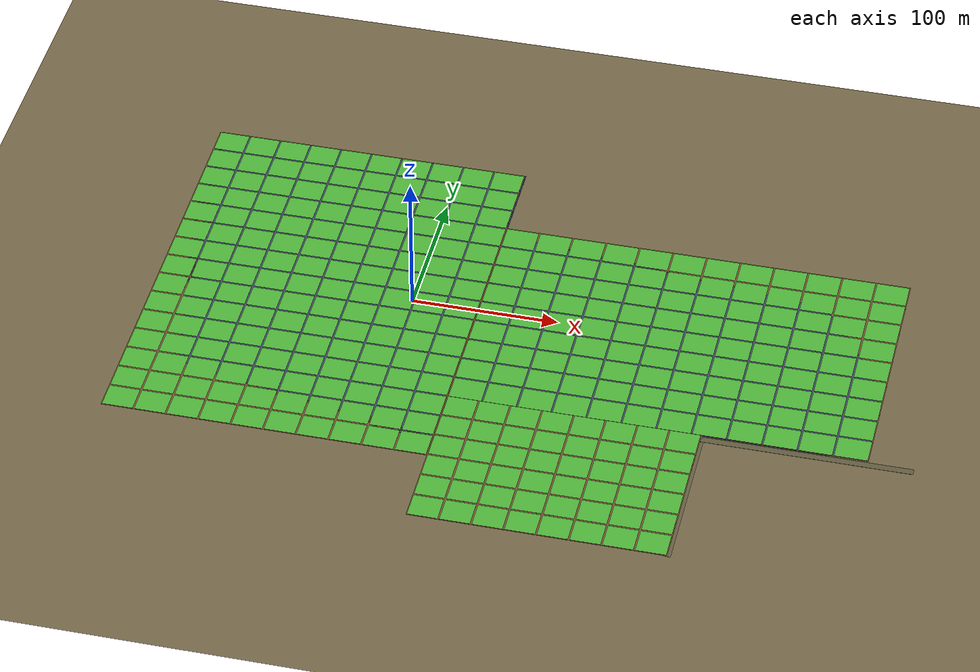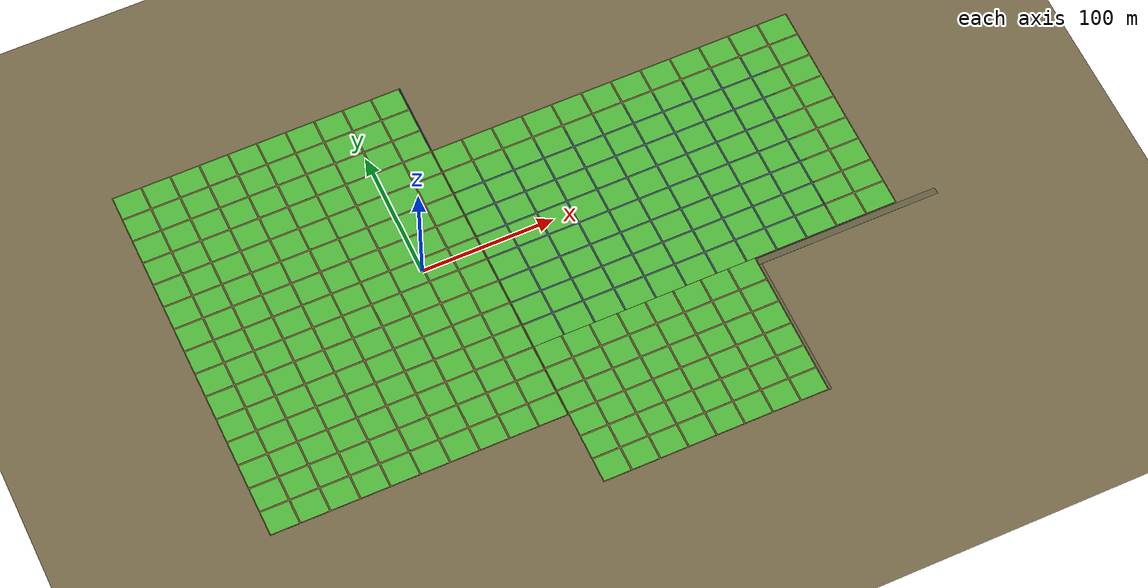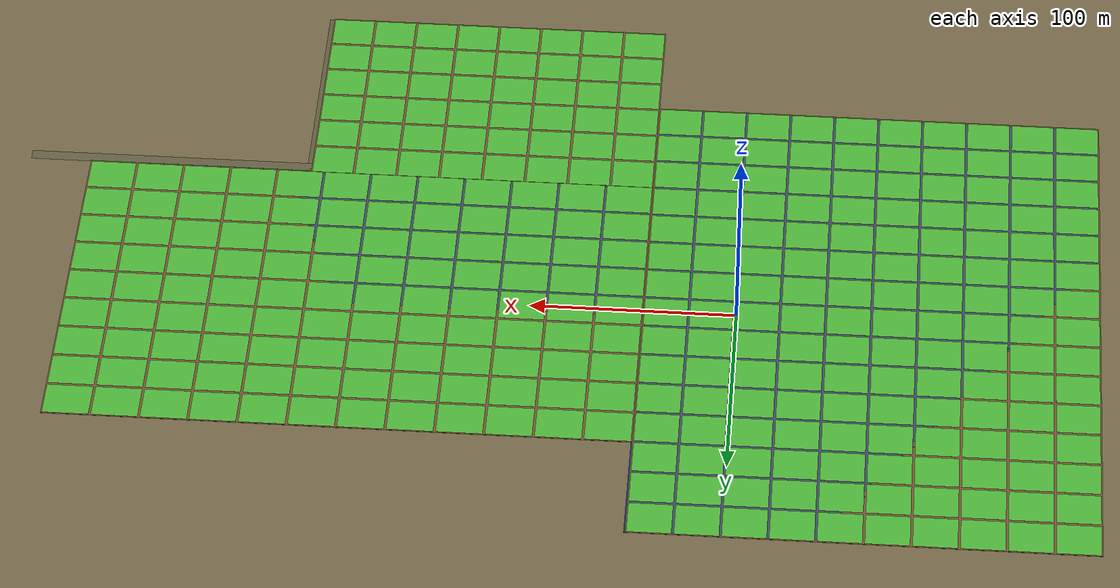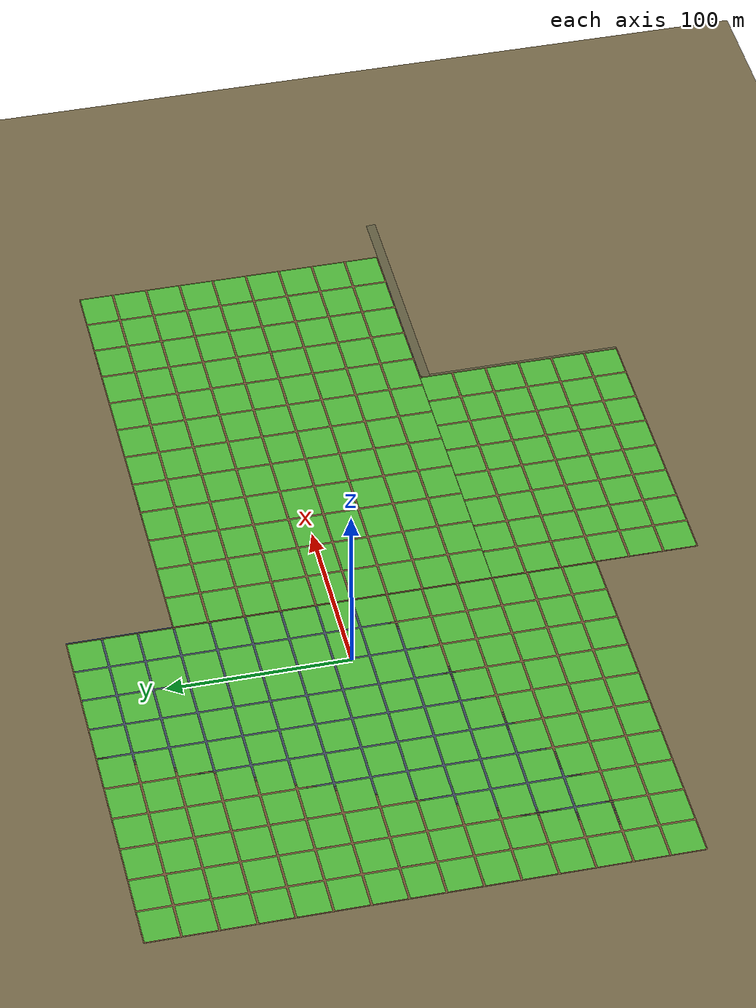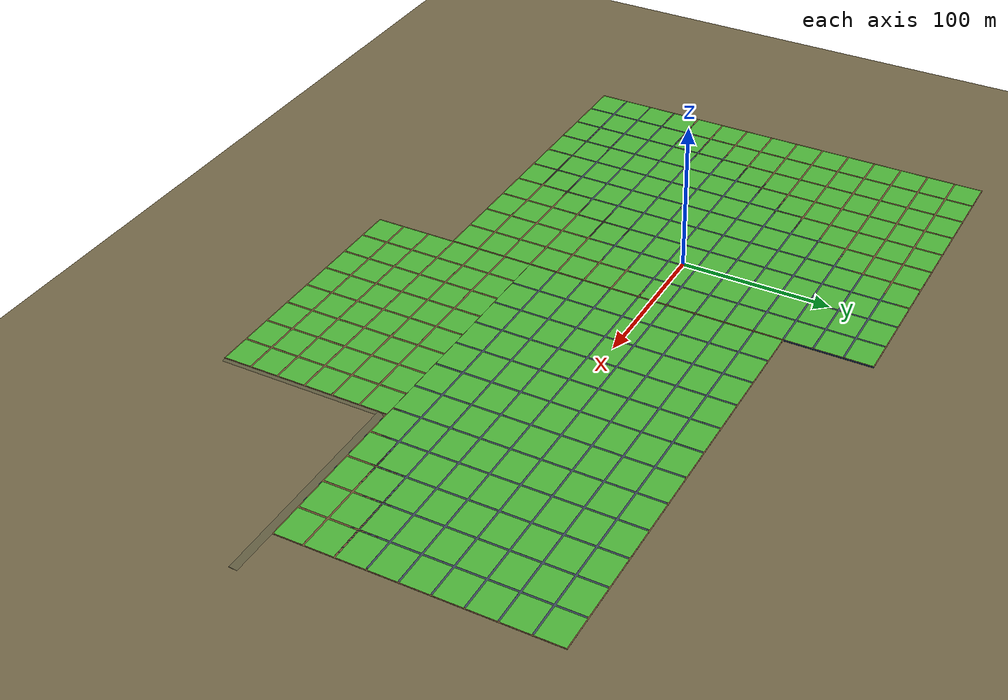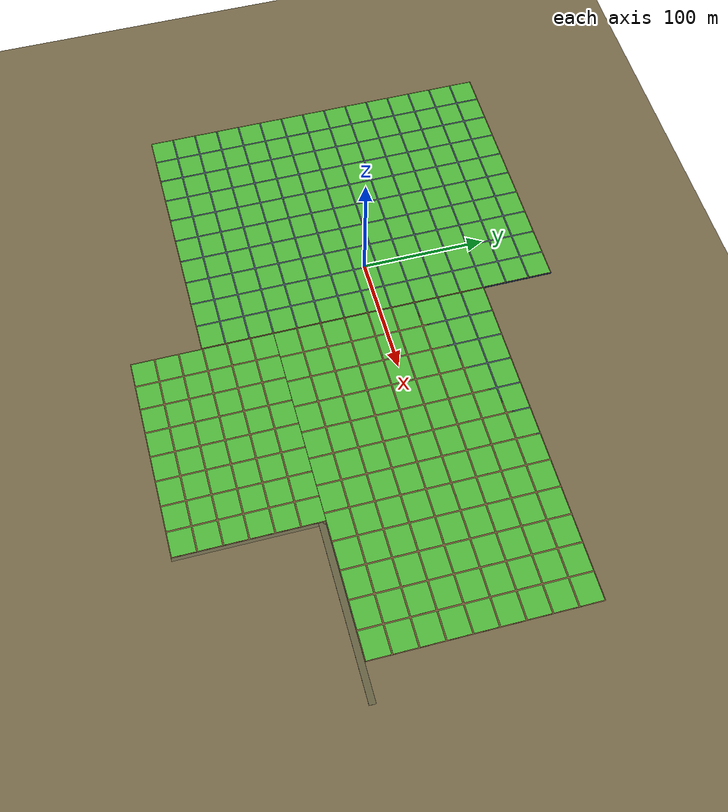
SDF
<sdf version="1.9">
 <world name="agricultural_field">
  <physics name="1ms" type="ignored">
   <max_step_size>0.001</max_step_size>
   <real_time_factor>1.0</real_time_factor>
   <real_time_update_rate>1000</real_time_update_rate>
  </physics>
  <wind><linear_velocity>1.5 1.5 0.0</linear_velocity></wind>
  <plugin filename="gz-sim-physics-system" name="gz::sim::systems::Physics"/>
  <plugin filename="gz-sim-user-commands-system" name="gz::sim::systems::UserCommands"/>
  <plugin filename="gz-sim-scene-broadcaster-system" name="gz::sim::systems::SceneBroadcaster"/>
  <plugin filename="gz-sim-sensors-system" name="gz::sim::systems::Sensors">
   <render_engine>ogre2</render_engine>
  </plugin>
  <plugin filename="gz-sim-imu-system" name="gz::sim::systems::Imu"/>
  <plugin filename="gz-sim-magnetometer-system" name="gz::sim::systems::Magnetometer"/>
  <plugin filename="gz-sim-navsat-system" name="gz::sim::systems::NavSat"/>
  <plugin filename="gz-sim-particle-emitter-system" name="gz::sim::systems::ParticleEmitter"/>
  <plugin filename="gz-sim-wind-effects-system" name="gz::sim::systems::WindEffects">
   <force_approximation_scaling_factor>1</force_approximation_scaling_factor>
   <horizontal>
    <magnitude>
     <time_for_rise>10</time_for_rise>
     <sin><amplitude_percent>0.05</amplitude_percent><period>60</period></sin>
     <noise type="gaussian"><mean>0</mean><stddev>0.0002</stddev></noise>
    </magnitude>
    <direction>
     <time_for_rise>30</time_for_rise>
     <sin><amplitude>5</amplitude><period>20</period></sin>
     <noise type="gaussian"><mean>0</mean><stddev>0.03</stddev></noise>
    </direction>
   </horizontal>
   <vertical><noise type="gaussian"><mean>0</mean><stddev>0.03</stddev></noise></vertical>
  </plugin>
  <scene>
   <ambient>0.85 0.85 0.85 1</ambient>
   <background>0.85 0.85 0.85 1</background>
   <shadows>true</shadows>
   <grid>false</grid>
   <origin_visual>false</origin_visual>
  </scene>
  <spherical_coordinates>
   <surface_model>EARTH_WGS84</surface_model>
   <latitude_deg>-6.8852</latitude_deg>
   <longitude_deg>107.5417</longitude_deg>
   <elevation>714</elevation>
   <heading_deg>0</heading_deg>
  </spherical_coordinates>
  <atmosphere type="adiabatic">
   <temperature>304</temperature>
   <pressure>93000</pressure>
   <temperature_gradient>-0.0065</temperature_gradient>
  </atmosphere>
  <wind><linear_velocity>1.5 0.5 0</linear_velocity></wind>
  <light type="directional" name="sun">
   <pose>0 0 100 0 0.4 -0.8</pose>
   <diffuse>1.0 0.95 0.85 1</diffuse>
   <specular>0.3 0.3 0.3 1</specular>
   <attenuation>
    <range>1000</range>
    <constant>0.9</constant>
    <linear>0.01</linear>
    <quadratic>0.001</quadratic>
   </attenuation>
   <direction>-0.5 0.2 -0.9</direction>
  </light>
  <light type="directional" name="sky_fill">
   <cast_shadows>false</cast_shadows>
   <pose>0 0 50 0 -1.57 0</pose>
   <diffuse>0.4 0.5 0.65 1</diffuse>
   <specular>0.0 0.0 0.0 1</specular>
   <direction>0 0 1</direction>
  </light>
  <model name="ground_base">
   <static>true</static>
   <link name="link">
    <collision name="col_1">
     <geometry><plane><normal>0 0 1</normal><size>500 500</size></plane></geometry>
     <surface><friction><ode><mu>0.8</mu><mu2>0.8</mu2></ode></friction></surface>
    </collision>
    <visual name="vis">
     <geometry><plane><normal>0 0 1</normal><size>500 500</size></plane></geometry>
     <material>
      <ambient>0.85 0.85 0.85 1</ambient>
      <diffuse>0.45 0.40 0.28 1</diffuse>
      <specular>0.05 0.05 0.05 1</specular>
     </material>
    </visual>
   </link>
  </model>
  <model name="sawah_kiri">
   <static>true</static>
   <pose>-65 0 0 0 0 0</pose>
   <link name="link">
    <visual name="soil_base">
     <geometry><box><size>220.00 290.00 0.10</size></box></geometry>
     <material><ambient>0.35 0.25 0.15 1</ambient><diffuse>0.45 0.32 0.20 1</diffuse></material>
    </visual>
    <visual name="plot_0">
     <pose>-99.00 -135.33 0.060 0 0 0</pose>
     <geometry><box><size>20.80 18.13 0.02</size></box></geometry>
     <material><ambient>0.20 0.50 0.15 1</ambient><diffuse>0.30 0.70 0.22 1</diffuse></material>
    </visual>
    <visual name="plot_1">
     <pose>-99.00 -116.00 0.060 0 0 0</pose>
     <geometry><box><size>20.80 18.13 0.02</size></box></geometry>
     <material><ambient>0.20 0.50 0.15 1</ambient><diffuse>0.30 0.70 0.22 1</diffuse></material>
    </visual>
    <visual name="plot_2">
     <pose>-99.00 -96.67 0.060 0 0 0</pose>
     <geometry><box><size>20.80 18.13 0.02</size></box></geometry>
     <material><ambient>0.20 0.50 0.15 1</ambient><diffuse>0.30 0.70 0.22 1</diffuse></material>
    </visual>
    <visual name="plot_3">
     <pose>-99.00 -77.33 0.060 0 0 0</pose>
     <geometry><box><size>20.80 18.13 0.02</size></box></geometry>
     <material><ambient>0.20 0.50 0.15 1</ambient><diffuse>0.30 0.70 0.22 1</diffuse></material>
    </visual>
    <visual name="plot_4">
     <pose>-99.00 -58.00 0.060 0 0 0</pose>
     <geometry><box><size>20.80 18.13 0.02</size></box></geometry>
     <material><ambient>0.20 0.50 0.15 1</ambient><diffuse>0.30 0.70 0.22 1</diffuse></material>
    </visual>
    <visual name="plot_5">
     <pose>-99.00 -38.67 0.060 0 0 0</pose>
     <geometry><box><size>20.80 18.13 0.02</size></box></geometry>
     <material><ambient>0.20 0.50 0.15 1</ambient><diffuse>0.30 0.70 0.22 1</diffuse></material>
    </visual>
    <visual name="plot_6">
     <pose>-99.00 -19.33 0.060 0 0 0</pose>
     <geometry><box><size>20.80 18.13 0.02</size></box></geometry>
     <material><ambient>0.20 0.50 0.15 1</ambient><diffuse>0.30 0.70 0.22 1</diffuse></material>
    </visual>
    <visual name="plot_7">
     <pose>-99.00 0.00 0.060 0 0 0</pose>
     <geometry><box><size>20.80 18.13 0.02</size></box></geometry>
     <material><ambient>0.20 0.50 0.15 1</ambient><diffuse>0.30 0.70 0.22 1</diffuse></material>
    </visual>
    <visual name="plot_8">
     <pose>-99.00 19.33 0.060 0 0 0</pose>
     <geometry><box><size>20.80 18.13 0.02</size></box></geometry>
     <material><ambient>0.20 0.50 0.15 1</ambient><diffuse>0.30 0.70 0.22 1</diffuse></material>
    </visual>
    <visual name="plot_9">
     <pose>-99.00 38.67 0.060 0 0 0</pose>
     <geometry><box><size>20.80 18.13 0.02</size></box></geometry>
     <material><ambient>0.20 0.50 0.15 1</ambient><diffuse>0.30 0.70 0.22 1</diffuse></material>
    </visual>
    <visual name="plot_10">
     <pose>-99.00 58.00 0.060 0 0 0</pose>
     <geometry><box><size>20.80 18.13 0.02</size></box></geometry>
     <material><ambient>0.20 0.50 0.15 1</ambient><diffuse>0.30 0.70 0.22 1</diffuse></material>
    </visual>
    <visual name="plot_11">
     <pose>-99.00 77.33 0.060 0 0 0</pose>
     <geometry><box><size>20.80 18.13 0.02</size></box></geometry>
     <material><ambient>0.20 0.50 0.15 1</ambient><diffuse>0.30 0.70 0.22 1</diffuse></material>
    </visual>
    <visual name="plot_12">
     <pose>-99.00 96.67 0.060 0 0 0</pose>
     <geometry><box><size>20.80 18.13 0.02</size></box></geometry>
     <material><ambient>0.20 0.50 0.15 1</ambient><diffuse>0.30 0.70 0.22 1</diffuse></material>
    </visual>
    <visual name="plot_13">
     <pose>-99.00 116.00 0.060 0 0 0</pose>
     <geometry><box><size>20.80 18.13 0.02</size></box></geometry>
     <material><ambient>0.20 0.50 0.15 1</ambient><diffuse>0.30 0.70 0.22 1</diffuse></material>
    </visual>
    <visual name="plot_14">
     <pose>-99.00 135.33 0.060 0 0 0</pose>
     <geometry><box><size>20.80 18.13 0.02</size></box></geometry>
     <material><ambient>0.20 0.50 0.15 1</ambient><diffuse>0.30 0.70 0.22 1</diffuse></material>
    </visual>
    <visual name="plot_15">
     <pose>-77.00 -135.33 0.060 0 0 0</pose>
     <geometry><box><size>20.80 18.13 0.02</size></box></geometry>
     <material><ambient>0.20 0.50 0.15 1</ambient><diffuse>0.30 0.70 0.22 1</diffuse></material>
    </visual>
    <visual name="plot_16">
     <pose>-77.00 -116.00 0.060 0 0 0</pose>
     <geometry><box><size>20.80 18.13 0.02</size></box></geometry>
     <material><ambient>0.20 0.50 0.15 1</ambient><diffuse>0.30 0.70 0.22 1</diffuse></material>
    </visual>
    <visual name="plot_17">
     <pose>-77.00 -96.67 0.060 0 0 0</pose>
     <geometry><box><size>20.80 18.13 0.02</size></box></geometry>
     <material><ambient>0.20 0.50 0.15 1</ambient><diffuse>0.30 0.70 0.22 1</diffuse></material>
    </visual>
    <visual name="plot_18">
     <pose>-77.00 -77.33 0.060 0 0 0</pose>
     <geometry><box><size>20.80 18.13 0.02</size></box></geometry>
     <material><ambient>0.20 0.50 0.15 1</ambient><diffuse>0.30 0.70 0.22 1</diffuse></material>
    </visual>
    <visual name="plot_19">
     <pose>-77.00 -58.00 0.060 0 0 0</pose>
     <geometry><box><size>20.80 18.13 0.02</size></box></geometry>
     <material><ambient>0.20 0.50 0.15 1</ambient><diffuse>0.30 0.70 0.22 1</diffuse></material>
    </visual>
    <visual name="plot_20">
     <pose>-77.00 -38.67 0.060 0 0 0</pose>
     <geometry><box><size>20.80 18.13 0.02</size></box></geometry>
     <material><ambient>0.20 0.50 0.15 1</ambient><diffuse>0.30 0.70 0.22 1</diffuse></material>
    </visual>
    <visual name="plot_21">
     <pose>-77.00 -19.33 0.060 0 0 0</pose>
     <geometry><box><size>20.80 18.13 0.02</size></box></geometry>
     <material><ambient>0.20 0.50 0.15 1</ambient><diffuse>0.30 0.70 0.22 1</diffuse></material>
    </visual>
    <visual name="plot_22">
     <pose>-77.00 0.00 0.060 0 0 0</pose>
     <geometry><box><size>20.80 18.13 0.02</size></box></geometry>
     <material><ambient>0.20 0.50 0.15 1</ambient><diffuse>0.30 0.70 0.22 1</diffuse></material>
    </visual>
    <visual name="plot_23">
     <pose>-77.00 19.33 0.060 0 0 0</pose>
     <geometry><box><size>20.80 18.13 0.02</size></box></geometry>
     <material><ambient>0.20 0.50 0.15 1</ambient><diffuse>0.30 0.70 0.22 1</diffuse></material>
    </visual>
    <visual name="plot_24">
     <pose>-77.00 38.67 0.060 0 0 0</pose>
     <geometry><box><size>20.80 18.13 0.02</size></box></geometry>
     <material><ambient>0.20 0.50 0.15 1</ambient><diffuse>0.30 0.70 0.22 1</diffuse></material>
    </visual>
    <visual name="plot_25">
     <pose>-77.00 58.00 0.060 0 0 0</pose>
     <geometry><box><size>20.80 18.13 0.02</size></box></geometry>
     <material><ambient>0.20 0.50 0.15 1</ambient><diffuse>0.30 0.70 0.22 1</diffuse></material>
    </visual>
    <visual name="plot_26">
     <pose>-77.00 77.33 0.060 0 0 0</pose>
     <geometry><box><size>20.80 18.13 0.02</size></box></geometry>
     <material><ambient>0.20 0.50 0.15 1</ambient><diffuse>0.30 0.70 0.22 1</diffuse></material>
    </visual>
    <visual name="plot_27">
     <pose>-77.00 96.67 0.060 0 0 0</pose>
     <geometry><box><size>20.80 18.13 0.02</size></box></geometry>
     <material><ambient>0.20 0.50 0.15 1</ambient><diffuse>0.30 0.70 0.22 1</diffuse></material>
    </visual>
    <visual name="plot_28">
     <pose>-77.00 116.00 0.060 0 0 0</pose>
     <geometry><box><size>20.80 18.13 0.02</size></box></geometry>
     <material><ambient>0.20 0.50 0.15 1</ambient><diffuse>0.30 0.70 0.22 1</diffuse></material>
    </visual>
    <visual name="plot_29">
     <pose>-77.00 135.33 0.060 0 0 0</pose>
     <geometry><box><size>20.80 18.13 0.02</size></box></geometry>
     <material><ambient>0.20 0.50 0.15 1</ambient><diffuse>0.30 0.70 0.22 1</diffuse></material>
    </visual>
    <visual name="plot_30">
     <pose>-55.00 -135.33 0.060 0 0 0</pose>
     <geometry><box><size>20.80 18.13 0.02</size></box></geometry>
     <material><ambient>0.20 0.50 0.15 1</ambient><diffuse>0.30 0.70 0.22 1</diffuse></material>
    </visual>
    <visual name="plot_31">
     <pose>-55.00 -116.00 0.060 0 0 0</pose>
     <geometry><box><size>20.80 18.13 0.02</size></box></geometry>
     <material><ambient>0.20 0.50 0.15 1</ambient><diffuse>0.30 0.70 0.22 1</diffuse></material>
    </visual>
    <visual name="plot_32">
     <pose>-55.00 -96.67 0.060 0 0 0</pose>
     <geometry><box><size>20.80 18.13 0.02</size></box></geometry>
     <material><ambient>0.20 0.50 0.15 1</ambient><diffuse>0.30 0.70 0.22 1</diffuse></material>
    </visual>
    <visual name="plot_33">
     <pose>-55.00 -77.33 0.060 0 0 0</pose>
     <geometry><box><size>20.80 18.13 0.02</size></box></geometry>
     <material><ambient>0.20 0.50 0.15 1</ambient><diffuse>0.30 0.70 0.22 1</diffuse></material>
    </visual>
    <visual name="plot_34">
     <pose>-55.00 -58.00 0.060 0 0 0</pose>
     <geometry><box><size>20.80 18.13 0.02</size></box></geometry>
     <material><ambient>0.20 0.50 0.15 1</ambient><diffuse>0.30 0.70 0.22 1</diffuse></material>
    </visual>
    <visual name="plot_35">
     <pose>-55.00 -38.67 0.060 0 0 0</pose>
     <geometry><box><size>20.80 18.13 0.02</size></box></geometry>
     <material><ambient>0.20 0.50 0.15 1</ambient><diffuse>0.30 0.70 0.22 1</diffuse></material>
    </visual>
    <visual name="plot_36">
     <pose>-55.00 -19.33 0.060 0 0 0</pose>
     <geometry><box><size>20.80 18.13 0.02</size></box></geometry>
     <material><ambient>0.20 0.50 0.15 1</ambient><diffuse>0.30 0.70 0.22 1</diffuse></material>
    </visual>
    <visual name="plot_37">
     <pose>-55.00 0.00 0.060 0 0 0</pose>
     <geometry><box><size>20.80 18.13 0.02</size></box></geometry>
     <material><ambient>0.20 0.50 0.15 1</ambient><diffuse>0.30 0.70 0.22 1</diffuse></material>
    </visual>
    <visual name="plot_38">
     <pose>-55.00 19.33 0.060 0 0 0</pose>
     <geometry><box><size>20.80 18.13 0.02</size></box></geometry>
     <material><ambient>0.20 0.50 0.15 1</ambient><diffuse>0.30 0.70 0.22 1</diffuse></material>
    </visual>
    <visual name="plot_39">
     <pose>-55.00 38.67 0.060 0 0 0</pose>
     <geometry><box><size>20.80 18.13 0.02</size></box></geometry>
     <material><ambient>0.20 0.50 0.15 1</ambient><diffuse>0.30 0.70 0.22 1</diffuse></material>
    </visual>
    <visual name="plot_40">
     <pose>-55.00 58.00 0.060 0 0 0</pose>
     <geometry><box><size>20.80 18.13 0.02</size></box></geometry>
     <material><ambient>0.20 0.50 0.15 1</ambient><diffuse>0.30 0.70 0.22 1</diffuse></material>
    </visual>
    <visual name="plot_41">
     <pose>-55.00 77.33 0.060 0 0 0</pose>
     <geometry><box><size>20.80 18.13 0.02</size></box></geometry>
     <material><ambient>0.20 0.50 0.15 1</ambient><diffuse>0.30 0.70 0.22 1</diffuse></material>
    </visual>
    <visual name="plot_42">
     <pose>-55.00 96.67 0.060 0 0 0</pose>
     <geometry><box><size>20.80 18.13 0.02</size></box></geometry>
     <material><ambient>0.20 0.50 0.15 1</ambient><diffuse>0.30 0.70 0.22 1</diffuse></material>
    </visual>
    <visual name="plot_43">
     <pose>-55.00 116.00 0.060 0 0 0</pose>
     <geometry><box><size>20.80 18.13 0.02</size></box></geometry>
     <material><ambient>0.20 0.50 0.15 1</ambient><diffuse>0.30 0.70 0.22 1</diffuse></material>
    </visual>
    <visual name="plot_44">
     <pose>-55.00 135.33 0.060 0 0 0</pose>
     <geometry><box><size>20.80 18.13 0.02</size></box></geometry>
     <material><ambient>0.20 0.50 0.15 1</ambient><diffuse>0.30 0.70 0.22 1</diffuse></material>
    </visual>
    <visual name="plot_45">
     <pose>-33.00 -135.33 0.060 0 0 0</pose>
     <geometry><box><size>20.80 18.13 0.02</size></box></geometry>
     <material><ambient>0.20 0.50 0.15 1</ambient><diffuse>0.30 0.70 0.22 1</diffuse></material>
    </visual>
    <visual name="plot_46">
     <pose>-33.00 -116.00 0.060 0 0 0</pose>
     <geometry><box><size>20.80 18.13 0.02</size></box></geometry>
     <material><ambient>0.20 0.50 0.15 1</ambient><diffuse>0.30 0.70 0.22 1</diffuse></material>
    </visual>
    <visual name="plot_47">
     <pose>-33.00 -96.67 0.060 0 0 0</pose>
     <geometry><box><size>20.80 18.13 0.02</size></box></geometry>
     <material><ambient>0.20 0.50 0.15 1</ambient><diffuse>0.30 0.70 0.22 1</diffuse></material>
    </visual>
    <visual name="plot_48">
     <pose>-33.00 -77.33 0.060 0 0 0</pose>
     <geometry><box><size>20.80 18.13 0.02</size></box></geometry>
     <material><ambient>0.20 0.50 0.15 1</ambient><diffuse>0.30 0.70 0.22 1</diffuse></material>
    </visual>
    <visual name="plot_49">
     <pose>-33.00 -58.00 0.060 0 0 0</pose>
     <geometry><box><size>20.80 18.13 0.02</size></box></geometry>
     <material><ambient>0.20 0.50 0.15 1</ambient><diffuse>0.30 0.70 0.22 1</diffuse></material>
    </visual>
    <visual name="plot_50">
     <pose>-33.00 -38.67 0.060 0 0 0</pose>
     <geometry><box><size>20.80 18.13 0.02</size></box></geometry>
     <material><ambient>0.20 0.50 0.15 1</ambient><diffuse>0.30 0.70 0.22 1</diffuse></material>
    </visual>
    <visual name="plot_51">
     <pose>-33.00 -19.33 0.060 0 0 0</pose>
     <geometry><box><size>20.80 18.13 0.02</size></box></geometry>
     <material><ambient>0.20 0.50 0.15 1</ambient><diffuse>0.30 0.70 0.22 1</diffuse></material>
    </visual>
    <visual name="plot_52">
     <pose>-33.00 0.00 0.060 0 0 0</pose>
     <geometry><box><size>20.80 18.13 0.02</size></box></geometry>
     <material><ambient>0.20 0.50 0.15 1</ambient><diffuse>0.30 0.70 0.22 1</diffuse></material>
    </visual>
    <visual name="plot_53">
     <pose>-33.00 19.33 0.060 0 0 0</pose>
     <geometry><box><size>20.80 18.13 0.02</size></box></geometry>
     <material><ambient>0.20 0.50 0.15 1</ambient><diffuse>0.30 0.70 0.22 1</diffuse></material>
    </visual>
    <visual name="plot_54">
     <pose>-33.00 38.67 0.060 0 0 0</pose>
     <geometry><box><size>20.80 18.13 0.02</size></box></geometry>
     <material><ambient>0.20 0.50 0.15 1</ambient><diffuse>0.30 0.70 0.22 1</diffuse></material>
    </visual>
    <visual name="plot_55">
     <pose>-33.00 58.00 0.060 0 0 0</pose>
     <geometry><box><size>20.80 18.13 0.02</size></box></geometry>
     <material><ambient>0.20 0.50 0.15 1</ambient><diffuse>0.30 0.70 0.22 1</diffuse></material>
    </visual>
    <visual name="plot_56">
     <pose>-33.00 77.33 0.060 0 0 0</pose>
     <geometry><box><size>20.80 18.13 0.02</size></box></geometry>
     <material><ambient>0.20 0.50 0.15 1</ambient><diffuse>0.30 0.70 0.22 1</diffuse></material>
    </visual>
    <visual name="plot_57">
     <pose>-33.00 96.67 0.060 0 0 0</pose>
     <geometry><box><size>20.80 18.13 0.02</size></box></geometry>
     <material><ambient>0.20 0.50 0.15 1</ambient><diffuse>0.30 0.70 0.22 1</diffuse></material>
    </visual>
    <visual name="plot_58">
     <pose>-33.00 116.00 0.060 0 0 0</pose>
     <geometry><box><size>20.80 18.13 0.02</size></box></geometry>
     <material><ambient>0.20 0.50 0.15 1</ambient><diffuse>0.30 0.70 0.22 1</diffuse></material>
    </visual>
    <visual name="plot_59">
     <pose>-33.00 135.33 0.060 0 0 0</pose>
     <geometry><box><size>20.80 18.13 0.02</size></box></geometry>
     <material><ambient>0.20 0.50 0.15 1</ambient><diffuse>0.30 0.70 0.22 1</diffuse></material>
    </visual>
    <visual name="plot_60">
     <pose>-11.00 -135.33 0.060 0 0 0</pose>
     <geometry><box><size>20.80 18.13 0.02</size></box></geometry>
     <material><ambient>0.20 0.50 0.15 1</ambient><diffuse>0.30 0.70 0.22 1</diffuse></material>
    </visual>
    <visual name="plot_61">
     <pose>-11.00 -116.00 0.060 0 0 0</pose>
     <geometry><box><size>20.80 18.13 0.02</size></box></geometry>
     <material><ambient>0.20 0.50 0.15 1</ambient><diffuse>0.30 0.70 0.22 1</diffuse></material>
    </visual>
    <visual name="plot_62">
     <pose>-11.00 -96.67 0.060 0 0 0</pose>
     <geometry><box><size>20.80 18.13 0.02</size></box></geometry>
     <material><ambient>0.20 0.50 0.15 1</ambient><diffuse>0.30 0.70 0.22 1</diffuse></material>
    </visual>
    <visual name="plot_63">
     <pose>-11.00 -77.33 0.060 0 0 0</pose>
     <geometry><box><size>20.80 18.13 0.02</size></box></geometry>
     <material><ambient>0.20 0.50 0.15 1</ambient><diffuse>0.30 0.70 0.22 1</diffuse></material>
    </visual>
    <visual name="plot_64">
     <pose>-11.00 -58.00 0.060 0 0 0</pose>
     <geometry><box><size>20.80 18.13 0.02</size></box></geometry>
     <material><ambient>0.20 0.50 0.15 1</ambient><diffuse>0.30 0.70 0.22 1</diffuse></material>
    </visual>
    <visual name="plot_65">
     <pose>-11.00 -38.67 0.060 0 0 0</pose>
     <geometry><box><size>20.80 18.13 0.02</size></box></geometry>
     <material><ambient>0.20 0.50 0.15 1</ambient><diffuse>0.30 0.70 0.22 1</diffuse></material>
    </visual>
    <visual name="plot_66">
     <pose>-11.00 -19.33 0.060 0 0 0</pose>
     <geometry><box><size>20.80 18.13 0.02</size></box></geometry>
     <material><ambient>0.20 0.50 0.15 1</ambient><diffuse>0.30 0.70 0.22 1</diffuse></material>
    </visual>
    <visual name="plot_67">
     <pose>-11.00 0.00 0.060 0 0 0</pose>
     <geometry><box><size>20.80 18.13 0.02</size></box></geometry>
     <material><ambient>0.20 0.50 0.15 1</ambient><diffuse>0.30 0.70 0.22 1</diffuse></material>
    </visual>
    <visual name="plot_68">
     <pose>-11.00 19.33 0.060 0 0 0</pose>
     <geometry><box><size>20.80 18.13 0.02</size></box></geometry>
     <material><ambient>0.20 0.50 0.15 1</ambient><diffuse>0.30 0.70 0.22 1</diffuse></material>
    </visual>
    <visual name="plot_69">
     <pose>-11.00 38.67 0.060 0 0 0</pose>
     <geometry><box><size>20.80 18.13 0.02</size></box></geometry>
     <material><ambient>0.20 0.50 0.15 1</ambient><diffuse>0.30 0.70 0.22 1</diffuse></material>
    </visual>
    <visual name="plot_70">
     <pose>-11.00 58.00 0.060 0 0 0</pose>
     <geometry><box><size>20.80 18.13 0.02</size></box></geometry>
     <material><ambient>0.20 0.50 0.15 1</ambient><diffuse>0.30 0.70 0.22 1</diffuse></material>
    </visual>
    <visual name="plot_71">
     <pose>-11.00 77.33 0.060 0 0 0</pose>
     <geometry><box><size>20.80 18.13 0.02</size></box></geometry>
     <material><ambient>0.20 0.50 0.15 1</ambient><diffuse>0.30 0.70 0.22 1</diffuse></material>
    </visual>
    <visual name="plot_72">
     <pose>-11.00 96.67 0.060 0 0 0</pose>
     <geometry><box><size>20.80 18.13 0.02</size></box></geometry>
     <material><ambient>0.20 0.50 0.15 1</ambient><diffuse>0.30 0.70 0.22 1</diffuse></material>
    </visual>
    <visual name="plot_73">
     <pose>-11.00 116.00 0.060 0 0 0</pose>
     <geometry><box><size>20.80 18.13 0.02</size></box></geometry>
     <material><ambient>0.20 0.50 0.15 1</ambient><diffuse>0.30 0.70 0.22 1</diffuse></material>
    </visual>
    <visual name="plot_74">
     <pose>-11.00 135.33 0.060 0 0 0</pose>
     <geometry><box><size>20.80 18.13 0.02</size></box></geometry>
     <material><ambient>0.20 0.50 0.15 1</ambient><diffuse>0.30 0.70 0.22 1</diffuse></material>
    </visual>
    <visual name="plot_75">
     <pose>11.00 -135.33 0.060 0 0 0</pose>
     <geometry><box><size>20.80 18.13 0.02</size></box></geometry>
     <material><ambient>0.20 0.50 0.15 1</ambient><diffuse>0.30 0.70 0.22 1</diffuse></material>
    </visual>
    <visual name="plot_76">
     <pose>11.00 -116.00 0.060 0 0 0</pose>
     <geometry><box><size>20.80 18.13 0.02</size></box></geometry>
     <material><ambient>0.20 0.50 0.15 1</ambient><diffuse>0.30 0.70 0.22 1</diffuse></material>
    </visual>
    <visual name="plot_77">
     <pose>11.00 -96.67 0.060 0 0 0</pose>
     <geometry><box><size>20.80 18.13 0.02</size></box></geometry>
     <material><ambient>0.20 0.50 0.15 1</ambient><diffuse>0.30 0.70 0.22 1</diffuse></material>
    </visual>
    <visual name="plot_78">
     <pose>11.00 -77.33 0.060 0 0 0</pose>
     <geometry><box><size>20.80 18.13 0.02</size></box></geometry>
     <material><ambient>0.20 0.50 0.15 1</ambient><diffuse>0.30 0.70 0.22 1</diffuse></material>
    </visual>
    <visual name="plot_79">
     <pose>11.00 -58.00 0.060 0 0 0</pose>
     <geometry><box><size>20.80 18.13 0.02</size></box></geometry>
     <material><ambient>0.20 0.50 0.15 1</ambient><diffuse>0.30 0.70 0.22 1</diffuse></material>
    </visual>
    <visual name="plot_80">
     <pose>11.00 -38.67 0.060 0 0 0</pose>
     <geometry><box><size>20.80 18.13 0.02</size></box></geometry>
     <material><ambient>0.20 0.50 0.15 1</ambient><diffuse>0.30 0.70 0.22 1</diffuse></material>
    </visual>
    <visual name="plot_81">
     <pose>11.00 -19.33 0.060 0 0 0</pose>
     <geometry><box><size>20.80 18.13 0.02</size></box></geometry>
     <material><ambient>0.20 0.50 0.15 1</ambient><diffuse>0.30 0.70 0.22 1</diffuse></material>
    </visual>
    <visual name="plot_82">
     <pose>11.00 0.00 0.060 0 0 0</pose>
     <geometry><box><size>20.80 18.13 0.02</size></box></geometry>
     <material><ambient>0.20 0.50 0.15 1</ambient><diffuse>0.30 0.70 0.22 1</diffuse></material>
    </visual>
    <visual name="plot_83">
     <pose>11.00 19.33 0.060 0 0 0</pose>
     <geometry><box><size>20.80 18.13 0.02</size></box></geometry>
     <material><ambient>0.20 0.50 0.15 1</ambient><diffuse>0.30 0.70 0.22 1</diffuse></material>
    </visual>
    <visual name="plot_84">
     <pose>11.00 38.67 0.060 0 0 0</pose>
     <geometry><box><size>20.80 18.13 0.02</size></box></geometry>
     <material><ambient>0.20 0.50 0.15 1</ambient><diffuse>0.30 0.70 0.22 1</diffuse></material>
    </visual>
    <visual name="plot_85">
     <pose>11.00 58.00 0.060 0 0 0</pose>
     <geometry><box><size>20.80 18.13 0.02</size></box></geometry>
     <material><ambient>0.20 0.50 0.15 1</ambient><diffuse>0.30 0.70 0.22 1</diffuse></material>
    </visual>
    <visual name="plot_86">
     <pose>11.00 77.33 0.060 0 0 0</pose>
     <geometry><box><size>20.80 18.13 0.02</size></box></geometry>
     <material><ambient>0.20 0.50 0.15 1</ambient><diffuse>0.30 0.70 0.22 1</diffuse></material>
    </visual>
    <visual name="plot_87">
     <pose>11.00 96.67 0.060 0 0 0</pose>
     <geometry><box><size>20.80 18.13 0.02</size></box></geometry>
     <material><ambient>0.20 0.50 0.15 1</ambient><diffuse>0.30 0.70 0.22 1</diffuse></material>
    </visual>
    <visual name="plot_88">
     <pose>11.00 116.00 0.060 0 0 0</pose>
     <geometry><box><size>20.80 18.13 0.02</size></box></geometry>
     <material><ambient>0.20 0.50 0.15 1</ambient><diffuse>0.30 0.70 0.22 1</diffuse></material>
    </visual>
    <visual name="plot_89">
     <pose>11.00 135.33 0.060 0 0 0</pose>
     <geometry><box><size>20.80 18.13 0.02</size></box></geometry>
     <material><ambient>0.20 0.50 0.15 1</ambient><diffuse>0.30 0.70 0.22 1</diffuse></material>
    </visual>
    <visual name="plot_90">
     <pose>33.00 -135.33 0.060 0 0 0</pose>
     <geometry><box><size>20.80 18.13 0.02</size></box></geometry>
     <material><ambient>0.20 0.50 0.15 1</ambient><diffuse>0.30 0.70 0.22 1</diffuse></material>
    </visual>
    <visual name="plot_91">
     <pose>33.00 -116.00 0.060 0 0 0</pose>
     <geometry><box><size>20.80 18.13 0.02</size></box></geometry>
     <material><ambient>0.20 0.50 0.15 1</ambient><diffuse>0.30 0.70 0.22 1</diffuse></material>
    </visual>
    <visual name="plot_92">
     <pose>33.00 -96.67 0.060 0 0 0</pose>
     <geometry><box><size>20.80 18.13 0.02</size></box></geometry>
     <material><ambient>0.20 0.50 0.15 1</ambient><diffuse>0.30 0.70 0.22 1</diffuse></material>
    </visual>
    <visual name="plot_93">
     <pose>33.00 -77.33 0.060 0 0 0</pose>
     <geometry><box><size>20.80 18.13 0.02</size></box></geometry>
     <material><ambient>0.20 0.50 0.15 1</ambient><diffuse>0.30 0.70 0.22 1</diffuse></material>
    </visual>
    <visual name="plot_94">
     <pose>33.00 -58.00 0.060 0 0 0</pose>
     <geometry><box><size>20.80 18.13 0.02</size></box></geometry>
     <material><ambient>0.20 0.50 0.15 1</ambient><diffuse>0.30 0.70 0.22 1</diffuse></material>
    </visual>
    <visual name="plot_95">
     <pose>33.00 -38.67 0.060 0 0 0</pose>
     <geometry><box><size>20.80 18.13 0.02</size></box></geometry>
     <material><ambient>0.20 0.50 0.15 1</ambient><diffuse>0.30 0.70 0.22 1</diffuse></material>
    </visual>
    <visual name="plot_96">
     <pose>33.00 -19.33 0.060 0 0 0</pose>
     <geometry><box><size>20.80 18.13 0.02</size></box></geometry>
     <material><ambient>0.20 0.50 0.15 1</ambient><diffuse>0.30 0.70 0.22 1</diffuse></material>
    </visual>
    <visual name="plot_97">
     <pose>33.00 0.00 0.060 0 0 0</pose>
     <geometry><box><size>20.80 18.13 0.02</size></box></geometry>
     <material><ambient>0.20 0.50 0.15 1</ambient><diffuse>0.30 0.70 0.22 1</diffuse></material>
    </visual>
    <visual name="plot_98">
     <pose>33.00 19.33 0.060 0 0 0</pose>
     <geometry><box><size>20.80 18.13 0.02</size></box></geometry>
     <material><ambient>0.20 0.50 0.15 1</ambient><diffuse>0.30 0.70 0.22 1</diffuse></material>
    </visual>
    <visual name="plot_99">
     <pose>33.00 38.67 0.060 0 0 0</pose>
     <geometry><box><size>20.80 18.13 0.02</size></box></geometry>
     <material><ambient>0.20 0.50 0.15 1</ambient><diffuse>0.30 0.70 0.22 1</diffuse></material>
    </visual>
    <visual name="plot_100">
     <pose>33.00 58.00 0.060 0 0 0</pose>
     <geometry><box><size>20.80 18.13 0.02</size></box></geometry>
     <material><ambient>0.20 0.50 0.15 1</ambient><diffuse>0.30 0.70 0.22 1</diffuse></material>
    </visual>
    <visual name="plot_101">
     <pose>33.00 77.33 0.060 0 0 0</pose>
     <geometry><box><size>20.80 18.13 0.02</size></box></geometry>
     <material><ambient>0.20 0.50 0.15 1</ambient><diffuse>0.30 0.70 0.22 1</diffuse></material>
    </visual>
    <visual name="plot_102">
     <pose>33.00 96.67 0.060 0 0 0</pose>
     <geometry><box><size>20.80 18.13 0.02</size></box></geometry>
     <material><ambient>0.20 0.50 0.15 1</ambient><diffuse>0.30 0.70 0.22 1</diffuse></material>
    </visual>
    <visual name="plot_103">
     <pose>33.00 116.00 0.060 0 0 0</pose>
     <geometry><box><size>20.80 18.13 0.02</size></box></geometry>
     <material><ambient>0.20 0.50 0.15 1</ambient><diffuse>0.30 0.70 0.22 1</diffuse></material>
    </visual>
    <visual name="plot_104">
     <pose>33.00 135.33 0.060 0 0 0</pose>
     <geometry><box><size>20.80 18.13 0.02</size></box></geometry>
     <material><ambient>0.20 0.50 0.15 1</ambient><diffuse>0.30 0.70 0.22 1</diffuse></material>
    </visual>
    <visual name="plot_105">
     <pose>55.00 -135.33 0.060 0 0 0</pose>
     <geometry><box><size>20.80 18.13 0.02</size></box></geometry>
     <material><ambient>0.20 0.50 0.15 1</ambient><diffuse>0.30 0.70 0.22 1</diffuse></material>
    </visual>
    <visual name="plot_106">
     <pose>55.00 -116.00 0.060 0 0 0</pose>
     <geometry><box><size>20.80 18.13 0.02</size></box></geometry>
     <material><ambient>0.20 0.50 0.15 1</ambient><diffuse>0.30 0.70 0.22 1</diffuse></material>
    </visual>
    <visual name="plot_107">
     <pose>55.00 -96.67 0.060 0 0 0</pose>
     <geometry><box><size>20.80 18.13 0.02</size></box></geometry>
     <material><ambient>0.20 0.50 0.15 1</ambient><diffuse>0.30 0.70 0.22 1</diffuse></material>
    </visual>
    <visual name="plot_108">
     <pose>55.00 -77.33 0.060 0 0 0</pose>
     <geometry><box><size>20.80 18.13 0.02</size></box></geometry>
     <material><ambient>0.20 0.50 0.15 1</ambient><diffuse>0.30 0.70 0.22 1</diffuse></material>
    </visual>
    <visual name="plot_109">
     <pose>55.00 -58.00 0.060 0 0 0</pose>
     <geometry><box><size>20.80 18.13 0.02</size></box></geometry>
     <material><ambient>0.20 0.50 0.15 1</ambient><diffuse>0.30 0.70 0.22 1</diffuse></material>
    </visual>
    <visual name="plot_110">
     <pose>55.00 -38.67 0.060 0 0 0</pose>
     <geometry><box><size>20.80 18.13 0.02</size></box></geometry>
     <material><ambient>0.20 0.50 0.15 1</ambient><diffuse>0.30 0.70 0.22 1</diffuse></material>
    </visual>
    <visual name="plot_111">
     <pose>55.00 -19.33 0.060 0 0 0</pose>
     <geometry><box><size>20.80 18.13 0.02</size></box></geometry>
     <material><ambient>0.20 0.50 0.15 1</ambient><diffuse>0.30 0.70 0.22 1</diffuse></material>
    </visual>
    <visual name="plot_112">
     <pose>55.00 0.00 0.060 0 0 0</pose>
     <geometry><box><size>20.80 18.13 0.02</size></box></geometry>
     <material><ambient>0.20 0.50 0.15 1</ambient><diffuse>0.30 0.70 0.22 1</diffuse></material>
    </visual>
    <visual name="plot_113">
     <pose>55.00 19.33 0.060 0 0 0</pose>
     <geometry><box><size>20.80 18.13 0.02</size></box></geometry>
     <material><ambient>0.20 0.50 0.15 1</ambient><diffuse>0.30 0.70 0.22 1</diffuse></material>
    </visual>
    <visual name="plot_114">
     <pose>55.00 38.67 0.060 0 0 0</pose>
     <geometry><box><size>20.80 18.13 0.02</size></box></geometry>
     <material><ambient>0.20 0.50 0.15 1</ambient><diffuse>0.30 0.70 0.22 1</diffuse></material>
    </visual>
    <visual name="plot_115">
     <pose>55.00 58.00 0.060 0 0 0</pose>
     <geometry><box><size>20.80 18.13 0.02</size></box></geometry>
     <material><ambient>0.20 0.50 0.15 1</ambient><diffuse>0.30 0.70 0.22 1</diffuse></material>
    </visual>
    <visual name="plot_116">
     <pose>55.00 77.33 0.060 0 0 0</pose>
     <geometry><box><size>20.80 18.13 0.02</size></box></geometry>
     <material><ambient>0.20 0.50 0.15 1</ambient><diffuse>0.30 0.70 0.22 1</diffuse></material>
    </visual>
    <visual name="plot_117">
     <pose>55.00 96.67 0.060 0 0 0</pose>
     <geometry><box><size>20.80 18.13 0.02</size></box></geometry>
     <material><ambient>0.20 0.50 0.15 1</ambient><diffuse>0.30 0.70 0.22 1</diffuse></material>
    </visual>
    <visual name="plot_118">
     <pose>55.00 116.00 0.060 0 0 0</pose>
     <geometry><box><size>20.80 18.13 0.02</size></box></geometry>
     <material><ambient>0.20 0.50 0.15 1</ambient><diffuse>0.30 0.70 0.22 1</diffuse></material>
    </visual>
    <visual name="plot_119">
     <pose>55.00 135.33 0.060 0 0 0</pose>
     <geometry><box><size>20.80 18.13 0.02</size></box></geometry>
     <material><ambient>0.20 0.50 0.15 1</ambient><diffuse>0.30 0.70 0.22 1</diffuse></material>
    </visual>
    <visual name="plot_120">
     <pose>77.00 -135.33 0.060 0 0 0</pose>
     <geometry><box><size>20.80 18.13 0.02</size></box></geometry>
     <material><ambient>0.20 0.50 0.15 1</ambient><diffuse>0.30 0.70 0.22 1</diffuse></material>
    </visual>
    <visual name="plot_121">
     <pose>77.00 -116.00 0.060 0 0 0</pose>
     <geometry><box><size>20.80 18.13 0.02</size></box></geometry>
     <material><ambient>0.20 0.50 0.15 1</ambient><diffuse>0.30 0.70 0.22 1</diffuse></material>
    </visual>
    <visual name="plot_122">
     <pose>77.00 -96.67 0.060 0 0 0</pose>
     <geometry><box><size>20.80 18.13 0.02</size></box></geometry>
     <material><ambient>0.20 0.50 0.15 1</ambient><diffuse>0.30 0.70 0.22 1</diffuse></material>
    </visual>
    <visual name="plot_123">
     <pose>77.00 -77.33 0.060 0 0 0</pose>
     <geometry><box><size>20.80 18.13 0.02</size></box></geometry>
     <material><ambient>0.20 0.50 0.15 1</ambient><diffuse>0.30 0.70 0.22 1</diffuse></material>
    </visual>
    <visual name="plot_124">
     <pose>77.00 -58.00 0.060 0 0 0</pose>
     <geometry><box><size>20.80 18.13 0.02</size></box></geometry>
     <material><ambient>0.20 0.50 0.15 1</ambient><diffuse>0.30 0.70 0.22 1</diffuse></material>
    </visual>
    <visual name="plot_125">
     <pose>77.00 -38.67 0.060 0 0 0</pose>
     <geometry><box><size>20.80 18.13 0.02</size></box></geometry>
     <material><ambient>0.20 0.50 0.15 1</ambient><diffuse>0.30 0.70 0.22 1</diffuse></material>
    </visual>
    <visual name="plot_126">
     <pose>77.00 -19.33 0.060 0 0 0</pose>
     <geometry><box><size>20.80 18.13 0.02</size></box></geometry>
     <material><ambient>0.20 0.50 0.15 1</ambient><diffuse>0.30 0.70 0.22 1</diffuse></material>
    </visual>
    <visual name="plot_127">
     <pose>77.00 0.00 0.060 0 0 0</pose>
     <geometry><box><size>20.80 18.13 0.02</size></box></geometry>
     <material><ambient>0.20 0.50 0.15 1</ambient><diffuse>0.30 0.70 0.22 1</diffuse></material>
    </visual>
    <visual name="plot_128">
     <pose>77.00 19.33 0.060 0 0 0</pose>
     <geometry><box><size>20.80 18.13 0.02</size></box></geometry>
     <material><ambient>0.20 0.50 0.15 1</ambient><diffuse>0.30 0.70 0.22 1</diffuse></material>
    </visual>
    <visual name="plot_129">
     <pose>77.00 38.67 0.060 0 0 0</pose>
     <geometry><box><size>20.80 18.13 0.02</size></box></geometry>
     <material><ambient>0.20 0.50 0.15 1</ambient><diffuse>0.30 0.70 0.22 1</diffuse></material>
    </visual>
    <visual name="plot_130">
     <pose>77.00 58.00 0.060 0 0 0</pose>
     <geometry><box><size>20.80 18.13 0.02</size></box></geometry>
     <material><ambient>0.20 0.50 0.15 1</ambient><diffuse>0.30 0.70 0.22 1</diffuse></material>
    </visual>
    <visual name="plot_131">
     <pose>77.00 77.33 0.060 0 0 0</pose>
     <geometry><box><size>20.80 18.13 0.02</size></box></geometry>
     <material><ambient>0.20 0.50 0.15 1</ambient><diffuse>0.30 0.70 0.22 1</diffuse></material>
    </visual>
    <visual name="plot_132">
     <pose>77.00 96.67 0.060 0 0 0</pose>
     <geometry><box><size>20.80 18.13 0.02</size></box></geometry>
     <material><ambient>0.20 0.50 0.15 1</ambient><diffuse>0.30 0.70 0.22 1</diffuse></material>
    </visual>
    <visual name="plot_133">
     <pose>77.00 116.00 0.060 0 0 0</pose>
     <geometry><box><size>20.80 18.13 0.02</size></box></geometry>
     <material><ambient>0.20 0.50 0.15 1</ambient><diffuse>0.30 0.70 0.22 1</diffuse></material>
    </visual>
    <visual name="plot_134">
     <pose>77.00 135.33 0.060 0 0 0</pose>
     <geometry><box><size>20.80 18.13 0.02</size></box></geometry>
     <material><ambient>0.20 0.50 0.15 1</ambient><diffuse>0.30 0.70 0.22 1</diffuse></material>
    </visual>
    <visual name="plot_135">
     <pose>99.00 -135.33 0.060 0 0 0</pose>
     <geometry><box><size>20.80 18.13 0.02</size></box></geometry>
     <material><ambient>0.20 0.50 0.15 1</ambient><diffuse>0.30 0.70 0.22 1</diffuse></material>
    </visual>
    <visual name="plot_136">
     <pose>99.00 -116.00 0.060 0 0 0</pose>
     <geometry><box><size>20.80 18.13 0.02</size></box></geometry>
     <material><ambient>0.20 0.50 0.15 1</ambient><diffuse>0.30 0.70 0.22 1</diffuse></material>
    </visual>
    <visual name="plot_137">
     <pose>99.00 -96.67 0.060 0 0 0</pose>
     <geometry><box><size>20.80 18.13 0.02</size></box></geometry>
     <material><ambient>0.20 0.50 0.15 1</ambient><diffuse>0.30 0.70 0.22 1</diffuse></material>
    </visual>
    <visual name="plot_138">
     <pose>99.00 -77.33 0.060 0 0 0</pose>
     <geometry><box><size>20.80 18.13 0.02</size></box></geometry>
     <material><ambient>0.20 0.50 0.15 1</ambient><diffuse>0.30 0.70 0.22 1</diffuse></material>
    </visual>
    <visual name="plot_139">
     <pose>99.00 -58.00 0.060 0 0 0</pose>
     <geometry><box><size>20.80 18.13 0.02</size></box></geometry>
     <material><ambient>0.20 0.50 0.15 1</ambient><diffuse>0.30 0.70 0.22 1</diffuse></material>
    </visual>
    <visual name="plot_140">
     <pose>99.00 -38.67 0.060 0 0 0</pose>
     <geometry><box><size>20.80 18.13 0.02</size></box></geometry>
     <material><ambient>0.20 0.50 0.15 1</ambient><diffuse>0.30 0.70 0.22 1</diffuse></material>
    </visual>
    <visual name="plot_141">
     <pose>99.00 -19.33 0.060 0 0 0</pose>
     <geometry><box><size>20.80 18.13 0.02</size></box></geometry>
     <material><ambient>0.20 0.50 0.15 1</ambient><diffuse>0.30 0.70 0.22 1</diffuse></material>
    </visual>
    <visual name="plot_142">
     <pose>99.00 0.00 0.060 0 0 0</pose>
     <geometry><box><size>20.80 18.13 0.02</size></box></geometry>
     <material><ambient>0.20 0.50 0.15 1</ambient><diffuse>0.30 0.70 0.22 1</diffuse></material>
    </visual>
    <visual name="plot_143">
     <pose>99.00 19.33 0.060 0 0 0</pose>
     <geometry><box><size>20.80 18.13 0.02</size></box></geometry>
     <material><ambient>0.20 0.50 0.15 1</ambient><diffuse>0.30 0.70 0.22 1</diffuse></material>
    </visual>
    <visual name="plot_144">
     <pose>99.00 38.67 0.060 0 0 0</pose>
     <geometry><box><size>20.80 18.13 0.02</size></box></geometry>
     <material><ambient>0.20 0.50 0.15 1</ambient><diffuse>0.30 0.70 0.22 1</diffuse></material>
    </visual>
    <visual name="plot_145">
     <pose>99.00 58.00 0.060 0 0 0</pose>
     <geometry><box><size>20.80 18.13 0.02</size></box></geometry>
     <material><ambient>0.20 0.50 0.15 1</ambient><diffuse>0.30 0.70 0.22 1</diffuse></material>
    </visual>
    <visual name="plot_146">
     <pose>99.00 77.33 0.060 0 0 0</pose>
     <geometry><box><size>20.80 18.13 0.02</size></box></geometry>
     <material><ambient>0.20 0.50 0.15 1</ambient><diffuse>0.30 0.70 0.22 1</diffuse></material>
    </visual>
    <visual name="plot_147">
     <pose>99.00 96.67 0.060 0 0 0</pose>
     <geometry><box><size>20.80 18.13 0.02</size></box></geometry>
     <material><ambient>0.20 0.50 0.15 1</ambient><diffuse>0.30 0.70 0.22 1</diffuse></material>
    </visual>
    <visual name="plot_148">
     <pose>99.00 116.00 0.060 0 0 0</pose>
     <geometry><box><size>20.80 18.13 0.02</size></box></geometry>
     <material><ambient>0.20 0.50 0.15 1</ambient><diffuse>0.30 0.70 0.22 1</diffuse></material>
    </visual>
    <visual name="plot_149">
     <pose>99.00 135.33 0.060 0 0 0</pose>
     <geometry><box><size>20.80 18.13 0.02</size></box></geometry>
     <material><ambient>0.20 0.50 0.15 1</ambient><diffuse>0.30 0.70 0.22 1</diffuse></material>
    </visual>
    <collision name="col_2"><geometry><box><size>220 290 0.1</size></box></geometry></collision>
   </link>
  </model>
  <model name="pematang_kiri_group">
   <static>true</static>
   <pose>-65 0 0.05 0 0 0</pose>
   <link name="row_01">
    <visual name="v">
     <pose>0 -135 0.075 0 0 0</pose>
     <geometry><box><size>0 0 0</size></box></geometry>
     <material><ambient>0.30 0.40 0.20 1</ambient><diffuse>0.35 0.50 0.25 1</diffuse></material>
    </visual>
   </link>
   <link name="row_02">
    <visual name="v">
     <pose>0 -117 0.075 0 0 0</pose>
     <geometry><box><size>0 0 0</size></box></geometry>
     <material><ambient>0.30 0.40 0.20 1</ambient><diffuse>0.35 0.50 0.25 1</diffuse></material>
    </visual>
   </link>
   <link name="row_03">
    <visual name="v">
     <pose>0 -99 0.075 0 0 0</pose>
     <geometry><box><size>0 0 0</size></box></geometry>
     <material><ambient>0.30 0.40 0.20 1</ambient><diffuse>0.35 0.50 0.25 1</diffuse></material>
    </visual>
   </link>
   <link name="row_04">
    <visual name="v">
     <pose>0 -81 0.075 0 0 0</pose>
     <geometry><box><size>0 0 0</size></box></geometry>
     <material><ambient>0.30 0.40 0.20 1</ambient><diffuse>0.35 0.50 0.25 1</diffuse></material>
    </visual>
   </link>
   <link name="row_05">
    <visual name="v">
     <pose>0 -63 0.075 0 0 0</pose>
     <geometry><box><size>0 0 0</size></box></geometry>
     <material><ambient>0.30 0.40 0.20 1</ambient><diffuse>0.35 0.50 0.25 1</diffuse></material>
    </visual>
   </link>
   <link name="row_06">
    <visual name="v">
     <pose>0 -45 0.075 0 0 0</pose>
     <geometry><box><size>0 0 0</size></box></geometry>
     <material><ambient>0.30 0.40 0.20 1</ambient><diffuse>0.35 0.50 0.25 1</diffuse></material>
    </visual>
   </link>
   <link name="row_07">
    <visual name="v">
     <pose>0 -27 0.075 0 0 0</pose>
     <geometry><box><size>0 0 0</size></box></geometry>
     <material><ambient>0.30 0.40 0.20 1</ambient><diffuse>0.35 0.50 0.25 1</diffuse></material>
    </visual>
   </link>
   <link name="row_08">
    <visual name="v">
     <pose>0  -9 0.075 0 0 0</pose>
     <geometry><box><size>0 0 0</size></box></geometry>
     <material><ambient>0.30 0.40 0.20 1</ambient><diffuse>0.35 0.50 0.25 1</diffuse></material>
    </visual>
   </link>
   <link name="row_09">
    <visual name="v">
     <pose>0   9 0.075 0 0 0</pose>
     <geometry><box><size>0 0 0</size></box></geometry>
     <material><ambient>0.30 0.40 0.20 1</ambient><diffuse>0.35 0.50 0.25 1</diffuse></material>
    </visual>
   </link>
   <link name="row_10">
    <visual name="v">
     <pose>0  27 0.075 0 0 0</pose>
     <geometry><box><size>0 0 0</size></box></geometry>
     <material><ambient>0.30 0.40 0.20 1</ambient><diffuse>0.35 0.50 0.25 1</diffuse></material>
    </visual>
   </link>
   <link name="row_11">
    <visual name="v">
     <pose>0  45 0.075 0 0 0</pose>
     <geometry><box><size>0 0 0</size></box></geometry>
     <material><ambient>0.30 0.40 0.20 1</ambient><diffuse>0.35 0.50 0.25 1</diffuse></material>
    </visual>
   </link>
   <link name="row_12">
    <visual name="v">
     <pose>0  63 0.075 0 0 0</pose>
     <geometry><box><size>0 0 0</size></box></geometry>
     <material><ambient>0.30 0.40 0.20 1</ambient><diffuse>0.35 0.50 0.25 1</diffuse></material>
    </visual>
   </link>
   <link name="row_13">
    <visual name="v">
     <pose>0  81 0.075 0 0 0</pose>
     <geometry><box><size>0 0 0</size></box></geometry>
     <material><ambient>0.30 0.40 0.20 1</ambient><diffuse>0.35 0.50 0.25 1</diffuse></material>
    </visual>
   </link>
   <link name="row_14">
    <visual name="v">
     <pose>0  99 0.075 0 0 0</pose>
     <geometry><box><size>0 0 0</size></box></geometry>
     <material><ambient>0.30 0.40 0.20 1</ambient><diffuse>0.35 0.50 0.25 1</diffuse></material>
    </visual>
   </link>
   <link name="row_15">
    <visual name="v">
     <pose>0 117 0.075 0 0 0</pose>
     <geometry><box><size>0 0 0</size></box></geometry>
     <material><ambient>0.30 0.40 0.20 1</ambient><diffuse>0.35 0.50 0.25 1</diffuse></material>
    </visual>
   </link>
   <link name="row_16">
    <visual name="v">
     <pose>0 135 0.075 0 0 0</pose>
     <geometry><box><size>0 0 0</size></box></geometry>
     <material><ambient>0.30 0.40 0.20 1</ambient><diffuse>0.35 0.50 0.25 1</diffuse></material>
    </visual>
   </link>
  </model>
  <model name="air_sawah_kiri">
   <static>true</static>
   <pose>-65 0 0.04 0 0 0</pose>
   <link name="link">
    <visual name="v">
     <geometry><box><size>218 288 0.02</size></box></geometry>
     <material>
      <ambient>0.10 0.25 0.45 0.55</ambient>
      <diffuse>0.12 0.30 0.55 0.55</diffuse>
      <specular>0.80 0.80 0.80 0.55</specular>
     </material>
     <transparency>0.45</transparency>
    </visual>
   </link>
  </model>
  <model name="sawah_kanan_atas">
   <static>true</static>
   <pose>185 0 0 0 0 0</pose>
   <link name="link">
    <visual name="soil_base">
     <geometry><box><size>280.00 175.00 0.10</size></box></geometry>
     <material><ambient>0.35 0.25 0.15 1</ambient><diffuse>0.45 0.32 0.20 1</diffuse></material>
    </visual>
    <visual name="plot_0">
     <pose>-128.33 -77.78 0.060 0 0 0</pose>
     <geometry><box><size>22.13 18.24 0.02</size></box></geometry>
     <material><ambient>0.20 0.50 0.15 1</ambient><diffuse>0.30 0.70 0.22 1</diffuse></material>
    </visual>
    <visual name="plot_1">
     <pose>-128.33 -58.33 0.060 0 0 0</pose>
     <geometry><box><size>22.13 18.24 0.02</size></box></geometry>
     <material><ambient>0.20 0.50 0.15 1</ambient><diffuse>0.30 0.70 0.22 1</diffuse></material>
    </visual>
    <visual name="plot_2">
     <pose>-128.33 -38.89 0.060 0 0 0</pose>
     <geometry><box><size>22.13 18.24 0.02</size></box></geometry>
     <material><ambient>0.20 0.50 0.15 1</ambient><diffuse>0.30 0.70 0.22 1</diffuse></material>
    </visual>
    <visual name="plot_3">
     <pose>-128.33 -19.44 0.060 0 0 0</pose>
     <geometry><box><size>22.13 18.24 0.02</size></box></geometry>
     <material><ambient>0.20 0.50 0.15 1</ambient><diffuse>0.30 0.70 0.22 1</diffuse></material>
    </visual>
    <visual name="plot_4">
     <pose>-128.33 0.00 0.060 0 0 0</pose>
     <geometry><box><size>22.13 18.24 0.02</size></box></geometry>
     <material><ambient>0.20 0.50 0.15 1</ambient><diffuse>0.30 0.70 0.22 1</diffuse></material>
    </visual>
    <visual name="plot_5">
     <pose>-128.33 19.44 0.060 0 0 0</pose>
     <geometry><box><size>22.13 18.24 0.02</size></box></geometry>
     <material><ambient>0.20 0.50 0.15 1</ambient><diffuse>0.30 0.70 0.22 1</diffuse></material>
    </visual>
    <visual name="plot_6">
     <pose>-128.33 38.89 0.060 0 0 0</pose>
     <geometry><box><size>22.13 18.24 0.02</size></box></geometry>
     <material><ambient>0.20 0.50 0.15 1</ambient><diffuse>0.30 0.70 0.22 1</diffuse></material>
    </visual>
    <visual name="plot_7">
     <pose>-128.33 58.33 0.060 0 0 0</pose>
     <geometry><box><size>22.13 18.24 0.02</size></box></geometry>
     <material><ambient>0.20 0.50 0.15 1</ambient><diffuse>0.30 0.70 0.22 1</diffuse></material>
    </visual>
    <visual name="plot_8">
     <pose>-128.33 77.78 0.060 0 0 0</pose>
     <geometry><box><size>22.13 18.24 0.02</size></box></geometry>
     <material><ambient>0.20 0.50 0.15 1</ambient><diffuse>0.30 0.70 0.22 1</diffuse></material>
    </visual>
    <visual name="plot_9">
     <pose>-105.00 -77.78 0.060 0 0 0</pose>
     <geometry><box><size>22.13 18.24 0.02</size></box></geometry>
     <material><ambient>0.20 0.50 0.15 1</ambient><diffuse>0.30 0.70 0.22 1</diffuse></material>
    </visual>
    <visual name="plot_10">
     <pose>-105.00 -58.33 0.060 0 0 0</pose>
     <geometry><box><size>22.13 18.24 0.02</size></box></geometry>
     <material><ambient>0.20 0.50 0.15 1</ambient><diffuse>0.30 0.70 0.22 1</diffuse></material>
    </visual>
    <visual name="plot_11">
     <pose>-105.00 -38.89 0.060 0 0 0</pose>
     <geometry><box><size>22.13 18.24 0.02</size></box></geometry>
     <material><ambient>0.20 0.50 0.15 1</ambient><diffuse>0.30 0.70 0.22 1</diffuse></material>
    </visual>
    <visual name="plot_12">
     <pose>-105.00 -19.44 0.060 0 0 0</pose>
     <geometry><box><size>22.13 18.24 0.02</size></box></geometry>
     <material><ambient>0.20 0.50 0.15 1</ambient><diffuse>0.30 0.70 0.22 1</diffuse></material>
    </visual>
    <visual name="plot_13">
     <pose>-105.00 0.00 0.060 0 0 0</pose>
     <geometry><box><size>22.13 18.24 0.02</size></box></geometry>
     <material><ambient>0.20 0.50 0.15 1</ambient><diffuse>0.30 0.70 0.22 1</diffuse></material>
    </visual>
    <visual name="plot_14">
     <pose>-105.00 19.44 0.060 0 0 0</pose>
     <geometry><box><size>22.13 18.24 0.02</size></box></geometry>
     <material><ambient>0.20 0.50 0.15 1</ambient><diffuse>0.30 0.70 0.22 1</diffuse></material>
    </visual>
    <visual name="plot_15">
     <pose>-105.00 38.89 0.060 0 0 0</pose>
     <geometry><box><size>22.13 18.24 0.02</size></box></geometry>
     <material><ambient>0.20 0.50 0.15 1</ambient><diffuse>0.30 0.70 0.22 1</diffuse></material>
    </visual>
    <visual name="plot_16">
     <pose>-105.00 58.33 0.060 0 0 0</pose>
     <geometry><box><size>22.13 18.24 0.02</size></box></geometry>
     <material><ambient>0.20 0.50 0.15 1</ambient><diffuse>0.30 0.70 0.22 1</diffuse></material>
    </visual>
    <visual name="plot_17">
     <pose>-105.00 77.78 0.060 0 0 0</pose>
     <geometry><box><size>22.13 18.24 0.02</size></box></geometry>
     <material><ambient>0.20 0.50 0.15 1</ambient><diffuse>0.30 0.70 0.22 1</diffuse></material>
    </visual>
    <visual name="plot_18">
     <pose>-81.67 -77.78 0.060 0 0 0</pose>
     <geometry><box><size>22.13 18.24 0.02</size></box></geometry>
     <material><ambient>0.20 0.50 0.15 1</ambient><diffuse>0.30 0.70 0.22 1</diffuse></material>
    </visual>
    <visual name="plot_19">
     <pose>-81.67 -58.33 0.060 0 0 0</pose>
     <geometry><box><size>22.13 18.24 0.02</size></box></geometry>
     <material><ambient>0.20 0.50 0.15 1</ambient><diffuse>0.30 0.70 0.22 1</diffuse></material>
    </visual>
    <visual name="plot_20">
     <pose>-81.67 -38.89 0.060 0 0 0</pose>
     <geometry><box><size>22.13 18.24 0.02</size></box></geometry>
     <material><ambient>0.20 0.50 0.15 1</ambient><diffuse>0.30 0.70 0.22 1</diffuse></material>
    </visual>
    <visual name="plot_21">
     <pose>-81.67 -19.44 0.060 0 0 0</pose>
     <geometry><box><size>22.13 18.24 0.02</size></box></geometry>
     <material><ambient>0.20 0.50 0.15 1</ambient><diffuse>0.30 0.70 0.22 1</diffuse></material>
    </visual>
    <visual name="plot_22">
     <pose>-81.67 0.00 0.060 0 0 0</pose>
     <geometry><box><size>22.13 18.24 0.02</size></box></geometry>
     <material><ambient>0.20 0.50 0.15 1</ambient><diffuse>0.30 0.70 0.22 1</diffuse></material>
    </visual>
    <visual name="plot_23">
     <pose>-81.67 19.44 0.060 0 0 0</pose>
     <geometry><box><size>22.13 18.24 0.02</size></box></geometry>
     <material><ambient>0.20 0.50 0.15 1</ambient><diffuse>0.30 0.70 0.22 1</diffuse></material>
    </visual>
    <visual name="plot_24">
     <pose>-81.67 38.89 0.060 0 0 0</pose>
     <geometry><box><size>22.13 18.24 0.02</size></box></geometry>
     <material><ambient>0.20 0.50 0.15 1</ambient><diffuse>0.30 0.70 0.22 1</diffuse></material>
    </visual>
    <visual name="plot_25">
     <pose>-81.67 58.33 0.060 0 0 0</pose>
     <geometry><box><size>22.13 18.24 0.02</size></box></geometry>
     <material><ambient>0.20 0.50 0.15 1</ambient><diffuse>0.30 0.70 0.22 1</diffuse></material>
    </visual>
    <visual name="plot_26">
     <pose>-81.67 77.78 0.060 0 0 0</pose>
     <geometry><box><size>22.13 18.24 0.02</size></box></geometry>
     <material><ambient>0.20 0.50 0.15 1</ambient><diffuse>0.30 0.70 0.22 1</diffuse></material>
    </visual>
    <visual name="plot_27">
     <pose>-58.33 -77.78 0.060 0 0 0</pose>
     <geometry><box><size>22.13 18.24 0.02</size></box></geometry>
     <material><ambient>0.20 0.50 0.15 1</ambient><diffuse>0.30 0.70 0.22 1</diffuse></material>
    </visual>
    <visual name="plot_28">
     <pose>-58.33 -58.33 0.060 0 0 0</pose>
     <geometry><box><size>22.13 18.24 0.02</size></box></geometry>
     <material><ambient>0.20 0.50 0.15 1</ambient><diffuse>0.30 0.70 0.22 1</diffuse></material>
    </visual>
    <visual name="plot_29">
     <pose>-58.33 -38.89 0.060 0 0 0</pose>
     <geometry><box><size>22.13 18.24 0.02</size></box></geometry>
     <material><ambient>0.20 0.50 0.15 1</ambient><diffuse>0.30 0.70 0.22 1</diffuse></material>
    </visual>
    <visual name="plot_30">
     <pose>-58.33 -19.44 0.060 0 0 0</pose>
     <geometry><box><size>22.13 18.24 0.02</size></box></geometry>
     <material><ambient>0.20 0.50 0.15 1</ambient><diffuse>0.30 0.70 0.22 1</diffuse></material>
    </visual>
    <visual name="plot_31">
     <pose>-58.33 0.00 0.060 0 0 0</pose>
     <geometry><box><size>22.13 18.24 0.02</size></box></geometry>
     <material><ambient>0.20 0.50 0.15 1</ambient><diffuse>0.30 0.70 0.22 1</diffuse></material>
    </visual>
    <visual name="plot_32">
     <pose>-58.33 19.44 0.060 0 0 0</pose>
     <geometry><box><size>22.13 18.24 0.02</size></box></geometry>
     <material><ambient>0.20 0.50 0.15 1</ambient><diffuse>0.30 0.70 0.22 1</diffuse></material>
    </visual>
    <visual name="plot_33">
     <pose>-58.33 38.89 0.060 0 0 0</pose>
     <geometry><box><size>22.13 18.24 0.02</size></box></geometry>
     <material><ambient>0.20 0.50 0.15 1</ambient><diffuse>0.30 0.70 0.22 1</diffuse></material>
    </visual>
    <visual name="plot_34">
     <pose>-58.33 58.33 0.060 0 0 0</pose>
     <geometry><box><size>22.13 18.24 0.02</size></box></geometry>
     <material><ambient>0.20 0.50 0.15 1</ambient><diffuse>0.30 0.70 0.22 1</diffuse></material>
    </visual>
    <visual name="plot_35">
     <pose>-58.33 77.78 0.060 0 0 0</pose>
     <geometry><box><size>22.13 18.24 0.02</size></box></geometry>
     <material><ambient>0.20 0.50 0.15 1</ambient><diffuse>0.30 0.70 0.22 1</diffuse></material>
    </visual>
    <visual name="plot_36">
     <pose>-35.00 -77.78 0.060 0 0 0</pose>
     <geometry><box><size>22.13 18.24 0.02</size></box></geometry>
     <material><ambient>0.20 0.50 0.15 1</ambient><diffuse>0.30 0.70 0.22 1</diffuse></material>
    </visual>
    <visual name="plot_37">
     <pose>-35.00 -58.33 0.060 0 0 0</pose>
     <geometry><box><size>22.13 18.24 0.02</size></box></geometry>
     <material><ambient>0.20 0.50 0.15 1</ambient><diffuse>0.30 0.70 0.22 1</diffuse></material>
    </visual>
    <visual name="plot_38">
     <pose>-35.00 -38.89 0.060 0 0 0</pose>
     <geometry><box><size>22.13 18.24 0.02</size></box></geometry>
     <material><ambient>0.20 0.50 0.15 1</ambient><diffuse>0.30 0.70 0.22 1</diffuse></material>
    </visual>
    <visual name="plot_39">
     <pose>-35.00 -19.44 0.060 0 0 0</pose>
     <geometry><box><size>22.13 18.24 0.02</size></box></geometry>
     <material><ambient>0.20 0.50 0.15 1</ambient><diffuse>0.30 0.70 0.22 1</diffuse></material>
    </visual>
    <visual name="plot_40">
     <pose>-35.00 0.00 0.060 0 0 0</pose>
     <geometry><box><size>22.13 18.24 0.02</size></box></geometry>
     <material><ambient>0.20 0.50 0.15 1</ambient><diffuse>0.30 0.70 0.22 1</diffuse></material>
    </visual>
    <visual name="plot_41">
     <pose>-35.00 19.44 0.060 0 0 0</pose>
     <geometry><box><size>22.13 18.24 0.02</size></box></geometry>
     <material><ambient>0.20 0.50 0.15 1</ambient><diffuse>0.30 0.70 0.22 1</diffuse></material>
    </visual>
    <visual name="plot_42">
     <pose>-35.00 38.89 0.060 0 0 0</pose>
     <geometry><box><size>22.13 18.24 0.02</size></box></geometry>
     <material><ambient>0.20 0.50 0.15 1</ambient><diffuse>0.30 0.70 0.22 1</diffuse></material>
    </visual>
    <visual name="plot_43">
     <pose>-35.00 58.33 0.060 0 0 0</pose>
     <geometry><box><size>22.13 18.24 0.02</size></box></geometry>
     <material><ambient>0.20 0.50 0.15 1</ambient><diffuse>0.30 0.70 0.22 1</diffuse></material>
    </visual>
    <visual name="plot_44">
     <pose>-35.00 77.78 0.060 0 0 0</pose>
     <geometry><box><size>22.13 18.24 0.02</size></box></geometry>
     <material><ambient>0.20 0.50 0.15 1</ambient><diffuse>0.30 0.70 0.22 1</diffuse></material>
    </visual>
    <visual name="plot_45">
     <pose>-11.67 -77.78 0.060 0 0 0</pose>
     <geometry><box><size>22.13 18.24 0.02</size></box></geometry>
     <material><ambient>0.20 0.50 0.15 1</ambient><diffuse>0.30 0.70 0.22 1</diffuse></material>
    </visual>
    <visual name="plot_46">
     <pose>-11.67 -58.33 0.060 0 0 0</pose>
     <geometry><box><size>22.13 18.24 0.02</size></box></geometry>
     <material><ambient>0.20 0.50 0.15 1</ambient><diffuse>0.30 0.70 0.22 1</diffuse></material>
    </visual>
    <visual name="plot_47">
     <pose>-11.67 -38.89 0.060 0 0 0</pose>
     <geometry><box><size>22.13 18.24 0.02</size></box></geometry>
     <material><ambient>0.20 0.50 0.15 1</ambient><diffuse>0.30 0.70 0.22 1</diffuse></material>
    </visual>
    <visual name="plot_48">
     <pose>-11.67 -19.44 0.060 0 0 0</pose>
     <geometry><box><size>22.13 18.24 0.02</size></box></geometry>
     <material><ambient>0.20 0.50 0.15 1</ambient><diffuse>0.30 0.70 0.22 1</diffuse></material>
    </visual>
    <visual name="plot_49">
     <pose>-11.67 0.00 0.060 0 0 0</pose>
     <geometry><box><size>22.13 18.24 0.02</size></box></geometry>
     <material><ambient>0.20 0.50 0.15 1</ambient><diffuse>0.30 0.70 0.22 1</diffuse></material>
    </visual>
    <visual name="plot_50">
     <pose>-11.67 19.44 0.060 0 0 0</pose>
     <geometry><box><size>22.13 18.24 0.02</size></box></geometry>
     <material><ambient>0.20 0.50 0.15 1</ambient><diffuse>0.30 0.70 0.22 1</diffuse></material>
    </visual>
    <visual name="plot_51">
     <pose>-11.67 38.89 0.060 0 0 0</pose>
     <geometry><box><size>22.13 18.24 0.02</size></box></geometry>
     <material><ambient>0.20 0.50 0.15 1</ambient><diffuse>0.30 0.70 0.22 1</diffuse></material>
    </visual>
    <visual name="plot_52">
     <pose>-11.67 58.33 0.060 0 0 0</pose>
     <geometry><box><size>22.13 18.24 0.02</size></box></geometry>
     <material><ambient>0.20 0.50 0.15 1</ambient><diffuse>0.30 0.70 0.22 1</diffuse></material>
    </visual>
    <visual name="plot_53">
     <pose>-11.67 77.78 0.060 0 0 0</pose>
     <geometry><box><size>22.13 18.24 0.02</size></box></geometry>
     <material><ambient>0.20 0.50 0.15 1</ambient><diffuse>0.30 0.70 0.22 1</diffuse></material>
    </visual>
    <visual name="plot_54">
     <pose>11.67 -77.78 0.060 0 0 0</pose>
     <geometry><box><size>22.13 18.24 0.02</size></box></geometry>
     <material><ambient>0.20 0.50 0.15 1</ambient><diffuse>0.30 0.70 0.22 1</diffuse></material>
    </visual>
    <visual name="plot_55">
     <pose>11.67 -58.33 0.060 0 0 0</pose>
     <geometry><box><size>22.13 18.24 0.02</size></box></geometry>
     <material><ambient>0.20 0.50 0.15 1</ambient><diffuse>0.30 0.70 0.22 1</diffuse></material>
    </visual>
    <visual name="plot_56">
     <pose>11.67 -38.89 0.060 0 0 0</pose>
     <geometry><box><size>22.13 18.24 0.02</size></box></geometry>
     <material><ambient>0.20 0.50 0.15 1</ambient><diffuse>0.30 0.70 0.22 1</diffuse></material>
    </visual>
    <visual name="plot_57">
     <pose>11.67 -19.44 0.060 0 0 0</pose>
     <geometry><box><size>22.13 18.24 0.02</size></box></geometry>
     <material><ambient>0.20 0.50 0.15 1</ambient><diffuse>0.30 0.70 0.22 1</diffuse></material>
    </visual>
    <visual name="plot_58">
     <pose>11.67 0.00 0.060 0 0 0</pose>
     <geometry><box><size>22.13 18.24 0.02</size></box></geometry>
     <material><ambient>0.20 0.50 0.15 1</ambient><diffuse>0.30 0.70 0.22 1</diffuse></material>
    </visual>
    <visual name="plot_59">
     <pose>11.67 19.44 0.060 0 0 0</pose>
     <geometry><box><size>22.13 18.24 0.02</size></box></geometry>
     <material><ambient>0.20 0.50 0.15 1</ambient><diffuse>0.30 0.70 0.22 1</diffuse></material>
    </visual>
    <visual name="plot_60">
     <pose>11.67 38.89 0.060 0 0 0</pose>
     <geometry><box><size>22.13 18.24 0.02</size></box></geometry>
     <material><ambient>0.20 0.50 0.15 1</ambient><diffuse>0.30 0.70 0.22 1</diffuse></material>
    </visual>
    <visual name="plot_61">
     <pose>11.67 58.33 0.060 0 0 0</pose>
     <geometry><box><size>22.13 18.24 0.02</size></box></geometry>
     <material><ambient>0.20 0.50 0.15 1</ambient><diffuse>0.30 0.70 0.22 1</diffuse></material>
    </visual>
    <visual name="plot_62">
     <pose>11.67 77.78 0.060 0 0 0</pose>
     <geometry><box><size>22.13 18.24 0.02</size></box></geometry>
     <material><ambient>0.20 0.50 0.15 1</ambient><diffuse>0.30 0.70 0.22 1</diffuse></material>
    </visual>
    <visual name="plot_63">
     <pose>35.00 -77.78 0.060 0 0 0</pose>
     <geometry><box><size>22.13 18.24 0.02</size></box></geometry>
     <material><ambient>0.20 0.50 0.15 1</ambient><diffuse>0.30 0.70 0.22 1</diffuse></material>
    </visual>
    <visual name="plot_64">
     <pose>35.00 -58.33 0.060 0 0 0</pose>
     <geometry><box><size>22.13 18.24 0.02</size></box></geometry>
     <material><ambient>0.20 0.50 0.15 1</ambient><diffuse>0.30 0.70 0.22 1</diffuse></material>
    </visual>
    <visual name="plot_65">
     <pose>35.00 -38.89 0.060 0 0 0</pose>
     <geometry><box><size>22.13 18.24 0.02</size></box></geometry>
     <material><ambient>0.20 0.50 0.15 1</ambient><diffuse>0.30 0.70 0.22 1</diffuse></material>
    </visual>
    <visual name="plot_66">
     <pose>35.00 -19.44 0.060 0 0 0</pose>
     <geometry><box><size>22.13 18.24 0.02</size></box></geometry>
     <material><ambient>0.20 0.50 0.15 1</ambient><diffuse>0.30 0.70 0.22 1</diffuse></material>
    </visual>
    <visual name="plot_67">
     <pose>35.00 0.00 0.060 0 0 0</pose>
     <geometry><box><size>22.13 18.24 0.02</size></box></geometry>
     <material><ambient>0.20 0.50 0.15 1</ambient><diffuse>0.30 0.70 0.22 1</diffuse></material>
    </visual>
    <visual name="plot_68">
     <pose>35.00 19.44 0.060 0 0 0</pose>
     <geometry><box><size>22.13 18.24 0.02</size></box></geometry>
     <material><ambient>0.20 0.50 0.15 1</ambient><diffuse>0.30 0.70 0.22 1</diffuse></material>
    </visual>
    <visual name="plot_69">
     <pose>35.00 38.89 0.060 0 0 0</pose>
     <geometry><box><size>22.13 18.24 0.02</size></box></geometry>
     <material><ambient>0.20 0.50 0.15 1</ambient><diffuse>0.30 0.70 0.22 1</diffuse></material>
    </visual>
    <visual name="plot_70">
     <pose>35.00 58.33 0.060 0 0 0</pose>
     <geometry><box><size>22.13 18.24 0.02</size></box></geometry>
     <material><ambient>0.20 0.50 0.15 1</ambient><diffuse>0.30 0.70 0.22 1</diffuse></material>
    </visual>
    <visual name="plot_71">
     <pose>35.00 77.78 0.060 0 0 0</pose>
     <geometry><box><size>22.13 18.24 0.02</size></box></geometry>
     <material><ambient>0.20 0.50 0.15 1</ambient><diffuse>0.30 0.70 0.22 1</diffuse></material>
    </visual>
    <visual name="plot_72">
     <pose>58.33 -77.78 0.060 0 0 0</pose>
     <geometry><box><size>22.13 18.24 0.02</size></box></geometry>
     <material><ambient>0.20 0.50 0.15 1</ambient><diffuse>0.30 0.70 0.22 1</diffuse></material>
    </visual>
    <visual name="plot_73">
     <pose>58.33 -58.33 0.060 0 0 0</pose>
     <geometry><box><size>22.13 18.24 0.02</size></box></geometry>
     <material><ambient>0.20 0.50 0.15 1</ambient><diffuse>0.30 0.70 0.22 1</diffuse></material>
    </visual>
    <visual name="plot_74">
     <pose>58.33 -38.89 0.060 0 0 0</pose>
     <geometry><box><size>22.13 18.24 0.02</size></box></geometry>
     <material><ambient>0.20 0.50 0.15 1</ambient><diffuse>0.30 0.70 0.22 1</diffuse></material>
    </visual>
    <visual name="plot_75">
     <pose>58.33 -19.44 0.060 0 0 0</pose>
     <geometry><box><size>22.13 18.24 0.02</size></box></geometry>
     <material><ambient>0.20 0.50 0.15 1</ambient><diffuse>0.30 0.70 0.22 1</diffuse></material>
    </visual>
    <visual name="plot_76">
     <pose>58.33 0.00 0.060 0 0 0</pose>
     <geometry><box><size>22.13 18.24 0.02</size></box></geometry>
     <material><ambient>0.20 0.50 0.15 1</ambient><diffuse>0.30 0.70 0.22 1</diffuse></material>
    </visual>
    <visual name="plot_77">
     <pose>58.33 19.44 0.060 0 0 0</pose>
     <geometry><box><size>22.13 18.24 0.02</size></box></geometry>
     <material><ambient>0.20 0.50 0.15 1</ambient><diffuse>0.30 0.70 0.22 1</diffuse></material>
    </visual>
    <visual name="plot_78">
     <pose>58.33 38.89 0.060 0 0 0</pose>
     <geometry><box><size>22.13 18.24 0.02</size></box></geometry>
     <material><ambient>0.20 0.50 0.15 1</ambient><diffuse>0.30 0.70 0.22 1</diffuse></material>
    </visual>
    <visual name="plot_79">
     <pose>58.33 58.33 0.060 0 0 0</pose>
     <geometry><box><size>22.13 18.24 0.02</size></box></geometry>
     <material><ambient>0.20 0.50 0.15 1</ambient><diffuse>0.30 0.70 0.22 1</diffuse></material>
    </visual>
    <visual name="plot_80">
     <pose>58.33 77.78 0.060 0 0 0</pose>
     <geometry><box><size>22.13 18.24 0.02</size></box></geometry>
     <material><ambient>0.20 0.50 0.15 1</ambient><diffuse>0.30 0.70 0.22 1</diffuse></material>
    </visual>
    <visual name="plot_81">
     <pose>81.67 -77.78 0.060 0 0 0</pose>
     <geometry><box><size>22.13 18.24 0.02</size></box></geometry>
     <material><ambient>0.20 0.50 0.15 1</ambient><diffuse>0.30 0.70 0.22 1</diffuse></material>
    </visual>
    <visual name="plot_82">
     <pose>81.67 -58.33 0.060 0 0 0</pose>
     <geometry><box><size>22.13 18.24 0.02</size></box></geometry>
     <material><ambient>0.20 0.50 0.15 1</ambient><diffuse>0.30 0.70 0.22 1</diffuse></material>
    </visual>
    <visual name="plot_83">
     <pose>81.67 -38.89 0.060 0 0 0</pose>
     <geometry><box><size>22.13 18.24 0.02</size></box></geometry>
     <material><ambient>0.20 0.50 0.15 1</ambient><diffuse>0.30 0.70 0.22 1</diffuse></material>
    </visual>
    <visual name="plot_84">
     <pose>81.67 -19.44 0.060 0 0 0</pose>
     <geometry><box><size>22.13 18.24 0.02</size></box></geometry>
     <material><ambient>0.20 0.50 0.15 1</ambient><diffuse>0.30 0.70 0.22 1</diffuse></material>
    </visual>
    <visual name="plot_85">
     <pose>81.67 0.00 0.060 0 0 0</pose>
     <geometry><box><size>22.13 18.24 0.02</size></box></geometry>
     <material><ambient>0.20 0.50 0.15 1</ambient><diffuse>0.30 0.70 0.22 1</diffuse></material>
    </visual>
    <visual name="plot_86">
     <pose>81.67 19.44 0.060 0 0 0</pose>
     <geometry><box><size>22.13 18.24 0.02</size></box></geometry>
     <material><ambient>0.20 0.50 0.15 1</ambient><diffuse>0.30 0.70 0.22 1</diffuse></material>
    </visual>
    <visual name="plot_87">
     <pose>81.67 38.89 0.060 0 0 0</pose>
     <geometry><box><size>22.13 18.24 0.02</size></box></geometry>
     <material><ambient>0.20 0.50 0.15 1</ambient><diffuse>0.30 0.70 0.22 1</diffuse></material>
    </visual>
    <visual name="plot_88">
     <pose>81.67 58.33 0.060 0 0 0</pose>
     <geometry><box><size>22.13 18.24 0.02</size></box></geometry>
     <material><ambient>0.20 0.50 0.15 1</ambient><diffuse>0.30 0.70 0.22 1</diffuse></material>
    </visual>
    <visual name="plot_89">
     <pose>81.67 77.78 0.060 0 0 0</pose>
     <geometry><box><size>22.13 18.24 0.02</size></box></geometry>
     <material><ambient>0.20 0.50 0.15 1</ambient><diffuse>0.30 0.70 0.22 1</diffuse></material>
    </visual>
    <visual name="plot_90">
     <pose>105.00 -77.78 0.060 0 0 0</pose>
     <geometry><box><size>22.13 18.24 0.02</size></box></geometry>
     <material><ambient>0.20 0.50 0.15 1</ambient><diffuse>0.30 0.70 0.22 1</diffuse></material>
    </visual>
    <visual name="plot_91">
     <pose>105.00 -58.33 0.060 0 0 0</pose>
     <geometry><box><size>22.13 18.24 0.02</size></box></geometry>
     <material><ambient>0.20 0.50 0.15 1</ambient><diffuse>0.30 0.70 0.22 1</diffuse></material>
    </visual>
    <visual name="plot_92">
     <pose>105.00 -38.89 0.060 0 0 0</pose>
     <geometry><box><size>22.13 18.24 0.02</size></box></geometry>
     <material><ambient>0.20 0.50 0.15 1</ambient><diffuse>0.30 0.70 0.22 1</diffuse></material>
    </visual>
    <visual name="plot_93">
     <pose>105.00 -19.44 0.060 0 0 0</pose>
     <geometry><box><size>22.13 18.24 0.02</size></box></geometry>
     <material><ambient>0.20 0.50 0.15 1</ambient><diffuse>0.30 0.70 0.22 1</diffuse></material>
    </visual>
    <visual name="plot_94">
     <pose>105.00 0.00 0.060 0 0 0</pose>
     <geometry><box><size>22.13 18.24 0.02</size></box></geometry>
     <material><ambient>0.20 0.50 0.15 1</ambient><diffuse>0.30 0.70 0.22 1</diffuse></material>
    </visual>
    <visual name="plot_95">
     <pose>105.00 19.44 0.060 0 0 0</pose>
     <geometry><box><size>22.13 18.24 0.02</size></box></geometry>
     <material><ambient>0.20 0.50 0.15 1</ambient><diffuse>0.30 0.70 0.22 1</diffuse></material>
    </visual>
    <visual name="plot_96">
     <pose>105.00 38.89 0.060 0 0 0</pose>
     <geometry><box><size>22.13 18.24 0.02</size></box></geometry>
     <material><ambient>0.20 0.50 0.15 1</ambient><diffuse>0.30 0.70 0.22 1</diffuse></material>
    </visual>
    <visual name="plot_97">
     <pose>105.00 58.33 0.060 0 0 0</pose>
     <geometry><box><size>22.13 18.24 0.02</size></box></geometry>
     <material><ambient>0.20 0.50 0.15 1</ambient><diffuse>0.30 0.70 0.22 1</diffuse></material>
    </visual>
    <visual name="plot_98">
     <pose>105.00 77.78 0.060 0 0 0</pose>
     <geometry><box><size>22.13 18.24 0.02</size></box></geometry>
     <material><ambient>0.20 0.50 0.15 1</ambient><diffuse>0.30 0.70 0.22 1</diffuse></material>
    </visual>
    <visual name="plot_99">
     <pose>128.33 -77.78 0.060 0 0 0</pose>
     <geometry><box><size>22.13 18.24 0.02</size></box></geometry>
     <material><ambient>0.20 0.50 0.15 1</ambient><diffuse>0.30 0.70 0.22 1</diffuse></material>
    </visual>
    <visual name="plot_100">
     <pose>128.33 -58.33 0.060 0 0 0</pose>
     <geometry><box><size>22.13 18.24 0.02</size></box></geometry>
     <material><ambient>0.20 0.50 0.15 1</ambient><diffuse>0.30 0.70 0.22 1</diffuse></material>
    </visual>
    <visual name="plot_101">
     <pose>128.33 -38.89 0.060 0 0 0</pose>
     <geometry><box><size>22.13 18.24 0.02</size></box></geometry>
     <material><ambient>0.20 0.50 0.15 1</ambient><diffuse>0.30 0.70 0.22 1</diffuse></material>
    </visual>
    <visual name="plot_102">
     <pose>128.33 -19.44 0.060 0 0 0</pose>
     <geometry><box><size>22.13 18.24 0.02</size></box></geometry>
     <material><ambient>0.20 0.50 0.15 1</ambient><diffuse>0.30 0.70 0.22 1</diffuse></material>
    </visual>
    <visual name="plot_103">
     <pose>128.33 0.00 0.060 0 0 0</pose>
     <geometry><box><size>22.13 18.24 0.02</size></box></geometry>
     <material><ambient>0.20 0.50 0.15 1</ambient><diffuse>0.30 0.70 0.22 1</diffuse></material>
    </visual>
    <visual name="plot_104">
     <pose>128.33 19.44 0.060 0 0 0</pose>
     <geometry><box><size>22.13 18.24 0.02</size></box></geometry>
     <material><ambient>0.20 0.50 0.15 1</ambient><diffuse>0.30 0.70 0.22 1</diffuse></material>
    </visual>
    <visual name="plot_105">
     <pose>128.33 38.89 0.060 0 0 0</pose>
     <geometry><box><size>22.13 18.24 0.02</size></box></geometry>
     <material><ambient>0.20 0.50 0.15 1</ambient><diffuse>0.30 0.70 0.22 1</diffuse></material>
    </visual>
    <visual name="plot_106">
     <pose>128.33 58.33 0.060 0 0 0</pose>
     <geometry><box><size>22.13 18.24 0.02</size></box></geometry>
     <material><ambient>0.20 0.50 0.15 1</ambient><diffuse>0.30 0.70 0.22 1</diffuse></material>
    </visual>
    <visual name="plot_107">
     <pose>128.33 77.78 0.060 0 0 0</pose>
     <geometry><box><size>22.13 18.24 0.02</size></box></geometry>
     <material><ambient>0.20 0.50 0.15 1</ambient><diffuse>0.30 0.70 0.22 1</diffuse></material>
    </visual>
    <collision name="col_3"><geometry><box><size>280 175 0.1</size></box></geometry></collision>
   </link>
  </model>
  <model name="pematang_kanan_atas">
   <static>true</static>
   <pose>185 0 0.05 0 0 0</pose>
   <link name="r1">
    <visual name="v">
     <pose>0 -72 0.075 0 0 0</pose>
     <geometry><box><size>0 0 0</size></box></geometry>
     <material><ambient>0.30 0.40 0.20 1</ambient><diffuse>0.35 0.50 0.25 1</diffuse></material>
    </visual>
   </link>
   <link name="r2">
    <visual name="v">
     <pose>0 -54 0.075 0 0 0</pose>
     <geometry><box><size>0 0 0</size></box></geometry>
     <material><ambient>0.30 0.40 0.20 1</ambient><diffuse>0.35 0.50 0.25 1</diffuse></material>
    </visual>
   </link>
   <link name="r3">
    <visual name="v">
     <pose>0 -36 0.075 0 0 0</pose>
     <geometry><box><size>0 0 0</size></box></geometry>
     <material><ambient>0.30 0.40 0.20 1</ambient><diffuse>0.35 0.50 0.25 1</diffuse></material>
    </visual>
   </link>
   <link name="r4">
    <visual name="v">
     <pose>0 -18 0.075 0 0 0</pose>
     <geometry><box><size>0 0 0</size></box></geometry>
     <material><ambient>0.30 0.40 0.20 1</ambient><diffuse>0.35 0.50 0.25 1</diffuse></material>
    </visual>
   </link>
   <link name="r5">
    <visual name="v">
     <pose>0   0 0.075 0 0 0</pose>
     <geometry><box><size>0 0 0</size></box></geometry>
     <material><ambient>0.30 0.40 0.20 1</ambient><diffuse>0.35 0.50 0.25 1</diffuse></material>
    </visual>
   </link>
   <link name="r6">
    <visual name="v">
     <pose>0  18 0.075 0 0 0</pose>
     <geometry><box><size>0 0 0</size></box></geometry>
     <material><ambient>0.30 0.40 0.20 1</ambient><diffuse>0.35 0.50 0.25 1</diffuse></material>
    </visual>
   </link>
   <link name="r7">
    <visual name="v">
     <pose>0  36 0.075 0 0 0</pose>
     <geometry><box><size>0 0 0</size></box></geometry>
     <material><ambient>0.30 0.40 0.20 1</ambient><diffuse>0.35 0.50 0.25 1</diffuse></material>
    </visual>
   </link>
   <link name="r8">
    <visual name="v">
     <pose>0  54 0.075 0 0 0</pose>
     <geometry><box><size>0 0 0</size></box></geometry>
     <material><ambient>0.30 0.40 0.20 1</ambient><diffuse>0.35 0.50 0.25 1</diffuse></material>
    </visual>
   </link>
   <link name="r9">
    <visual name="v">
     <pose>0  72 0.075 0 0 0</pose>
     <geometry><box><size>0 0 0</size></box></geometry>
     <material><ambient>0.30 0.40 0.20 1</ambient><diffuse>0.35 0.50 0.25 1</diffuse></material>
    </visual>
   </link>
  </model>
  <model name="air_sawah_kanan_atas">
   <static>true</static>
   <pose>185 0 0.04 0 0 0</pose>
   <link name="link">
    <visual name="v">
     <geometry><box><size>278 173 0.02</size></box></geometry>
     <material>
      <ambient>0.10 0.25 0.45 0.55</ambient>
      <diffuse>0.12 0.30 0.55 0.55</diffuse>
      <specular>0.80 0.80 0.80 0.55</specular>
     </material>
     <transparency>0.45</transparency>
    </visual>
   </link>
  </model>
  <model name="sawah_tengah_bawah">
   <static>true</static>
   <pose>130 -144 0 0 0 0</pose>
   <link name="link">
    <visual name="soil_base">
     <geometry><box><size>170.00 115.00 0.10</size></box></geometry>
     <material><ambient>0.35 0.25 0.15 1</ambient><diffuse>0.45 0.32 0.20 1</diffuse></material>
    </visual>
    <visual name="plot_0">
     <pose>-74.38 -47.92 0.060 0 0 0</pose>
     <geometry><box><size>20.05 17.97 0.02</size></box></geometry>
     <material><ambient>0.20 0.50 0.15 1</ambient><diffuse>0.30 0.70 0.22 1</diffuse></material>
    </visual>
    <visual name="plot_1">
     <pose>-74.38 -28.75 0.060 0 0 0</pose>
     <geometry><box><size>20.05 17.97 0.02</size></box></geometry>
     <material><ambient>0.20 0.50 0.15 1</ambient><diffuse>0.30 0.70 0.22 1</diffuse></material>
    </visual>
    <visual name="plot_2">
     <pose>-74.38 -9.58 0.060 0 0 0</pose>
     <geometry><box><size>20.05 17.97 0.02</size></box></geometry>
     <material><ambient>0.20 0.50 0.15 1</ambient><diffuse>0.30 0.70 0.22 1</diffuse></material>
    </visual>
    <visual name="plot_3">
     <pose>-74.38 9.58 0.060 0 0 0</pose>
     <geometry><box><size>20.05 17.97 0.02</size></box></geometry>
     <material><ambient>0.20 0.50 0.15 1</ambient><diffuse>0.30 0.70 0.22 1</diffuse></material>
    </visual>
    <visual name="plot_4">
     <pose>-74.38 28.75 0.060 0 0 0</pose>
     <geometry><box><size>20.05 17.97 0.02</size></box></geometry>
     <material><ambient>0.20 0.50 0.15 1</ambient><diffuse>0.30 0.70 0.22 1</diffuse></material>
    </visual>
    <visual name="plot_5">
     <pose>-74.38 47.92 0.060 0 0 0</pose>
     <geometry><box><size>20.05 17.97 0.02</size></box></geometry>
     <material><ambient>0.20 0.50 0.15 1</ambient><diffuse>0.30 0.70 0.22 1</diffuse></material>
    </visual>
    <visual name="plot_6">
     <pose>-53.12 -47.92 0.060 0 0 0</pose>
     <geometry><box><size>20.05 17.97 0.02</size></box></geometry>
     <material><ambient>0.20 0.50 0.15 1</ambient><diffuse>0.30 0.70 0.22 1</diffuse></material>
    </visual>
    <visual name="plot_7">
     <pose>-53.12 -28.75 0.060 0 0 0</pose>
     <geometry><box><size>20.05 17.97 0.02</size></box></geometry>
     <material><ambient>0.20 0.50 0.15 1</ambient><diffuse>0.30 0.70 0.22 1</diffuse></material>
    </visual>
    <visual name="plot_8">
     <pose>-53.12 -9.58 0.060 0 0 0</pose>
     <geometry><box><size>20.05 17.97 0.02</size></box></geometry>
     <material><ambient>0.20 0.50 0.15 1</ambient><diffuse>0.30 0.70 0.22 1</diffuse></material>
    </visual>
    <visual name="plot_9">
     <pose>-53.12 9.58 0.060 0 0 0</pose>
     <geometry><box><size>20.05 17.97 0.02</size></box></geometry>
     <material><ambient>0.20 0.50 0.15 1</ambient><diffuse>0.30 0.70 0.22 1</diffuse></material>
    </visual>
    <visual name="plot_10">
     <pose>-53.12 28.75 0.060 0 0 0</pose>
     <geometry><box><size>20.05 17.97 0.02</size></box></geometry>
     <material><ambient>0.20 0.50 0.15 1</ambient><diffuse>0.30 0.70 0.22 1</diffuse></material>
    </visual>
    <visual name="plot_11">
     <pose>-53.12 47.92 0.060 0 0 0</pose>
     <geometry><box><size>20.05 17.97 0.02</size></box></geometry>
     <material><ambient>0.20 0.50 0.15 1</ambient><diffuse>0.30 0.70 0.22 1</diffuse></material>
    </visual>
    <visual name="plot_12">
     <pose>-31.88 -47.92 0.060 0 0 0</pose>
     <geometry><box><size>20.05 17.97 0.02</size></box></geometry>
     <material><ambient>0.20 0.50 0.15 1</ambient><diffuse>0.30 0.70 0.22 1</diffuse></material>
    </visual>
    <visual name="plot_13">
     <pose>-31.88 -28.75 0.060 0 0 0</pose>
     <geometry><box><size>20.05 17.97 0.02</size></box></geometry>
     <material><ambient>0.20 0.50 0.15 1</ambient><diffuse>0.30 0.70 0.22 1</diffuse></material>
    </visual>
    <visual name="plot_14">
     <pose>-31.88 -9.58 0.060 0 0 0</pose>
     <geometry><box><size>20.05 17.97 0.02</size></box></geometry>
     <material><ambient>0.20 0.50 0.15 1</ambient><diffuse>0.30 0.70 0.22 1</diffuse></material>
    </visual>
    <visual name="plot_15">
     <pose>-31.88 9.58 0.060 0 0 0</pose>
     <geometry><box><size>20.05 17.97 0.02</size></box></geometry>
     <material><ambient>0.20 0.50 0.15 1</ambient><diffuse>0.30 0.70 0.22 1</diffuse></material>
    </visual>
    <visual name="plot_16">
     <pose>-31.88 28.75 0.060 0 0 0</pose>
     <geometry><box><size>20.05 17.97 0.02</size></box></geometry>
     <material><ambient>0.20 0.50 0.15 1</ambient><diffuse>0.30 0.70 0.22 1</diffuse></material>
    </visual>
    <visual name="plot_17">
     <pose>-31.88 47.92 0.060 0 0 0</pose>
     <geometry><box><size>20.05 17.97 0.02</size></box></geometry>
     <material><ambient>0.20 0.50 0.15 1</ambient><diffuse>0.30 0.70 0.22 1</diffuse></material>
    </visual>
    <visual name="plot_18">
     <pose>-10.62 -47.92 0.060 0 0 0</pose>
     <geometry><box><size>20.05 17.97 0.02</size></box></geometry>
     <material><ambient>0.20 0.50 0.15 1</ambient><diffuse>0.30 0.70 0.22 1</diffuse></material>
    </visual>
    <visual name="plot_19">
     <pose>-10.62 -28.75 0.060 0 0 0</pose>
     <geometry><box><size>20.05 17.97 0.02</size></box></geometry>
     <material><ambient>0.20 0.50 0.15 1</ambient><diffuse>0.30 0.70 0.22 1</diffuse></material>
    </visual>
    <visual name="plot_20">
     <pose>-10.62 -9.58 0.060 0 0 0</pose>
     <geometry><box><size>20.05 17.97 0.02</size></box></geometry>
     <material><ambient>0.20 0.50 0.15 1</ambient><diffuse>0.30 0.70 0.22 1</diffuse></material>
    </visual>
    <visual name="plot_21">
     <pose>-10.62 9.58 0.060 0 0 0</pose>
     <geometry><box><size>20.05 17.97 0.02</size></box></geometry>
     <material><ambient>0.20 0.50 0.15 1</ambient><diffuse>0.30 0.70 0.22 1</diffuse></material>
    </visual>
    <visual name="plot_22">
     <pose>-10.62 28.75 0.060 0 0 0</pose>
     <geometry><box><size>20.05 17.97 0.02</size></box></geometry>
     <material><ambient>0.20 0.50 0.15 1</ambient><diffuse>0.30 0.70 0.22 1</diffuse></material>
    </visual>
    <visual name="plot_23">
     <pose>-10.62 47.92 0.060 0 0 0</pose>
     <geometry><box><size>20.05 17.97 0.02</size></box></geometry>
     <material><ambient>0.20 0.50 0.15 1</ambient><diffuse>0.30 0.70 0.22 1</diffuse></material>
    </visual>
    <visual name="plot_24">
     <pose>10.62 -47.92 0.060 0 0 0</pose>
     <geometry><box><size>20.05 17.97 0.02</size></box></geometry>
     <material><ambient>0.20 0.50 0.15 1</ambient><diffuse>0.30 0.70 0.22 1</diffuse></material>
    </visual>
    <visual name="plot_25">
     <pose>10.62 -28.75 0.060 0 0 0</pose>
     <geometry><box><size>20.05 17.97 0.02</size></box></geometry>
     <material><ambient>0.20 0.50 0.15 1</ambient><diffuse>0.30 0.70 0.22 1</diffuse></material>
    </visual>
    <visual name="plot_26">
     <pose>10.62 -9.58 0.060 0 0 0</pose>
     <geometry><box><size>20.05 17.97 0.02</size></box></geometry>
     <material><ambient>0.20 0.50 0.15 1</ambient><diffuse>0.30 0.70 0.22 1</diffuse></material>
    </visual>
    <visual name="plot_27">
     <pose>10.62 9.58 0.060 0 0 0</pose>
     <geometry><box><size>20.05 17.97 0.02</size></box></geometry>
     <material><ambient>0.20 0.50 0.15 1</ambient><diffuse>0.30 0.70 0.22 1</diffuse></material>
    </visual>
    <visual name="plot_28">
     <pose>10.62 28.75 0.060 0 0 0</pose>
     <geometry><box><size>20.05 17.97 0.02</size></box></geometry>
     <material><ambient>0.20 0.50 0.15 1</ambient><diffuse>0.30 0.70 0.22 1</diffuse></material>
    </visual>
    <visual name="plot_29">
     <pose>10.62 47.92 0.060 0 0 0</pose>
     <geometry><box><size>20.05 17.97 0.02</size></box></geometry>
     <material><ambient>0.20 0.50 0.15 1</ambient><diffuse>0.30 0.70 0.22 1</diffuse></material>
    </visual>
    <visual name="plot_30">
     <pose>31.88 -47.92 0.060 0 0 0</pose>
     <geometry><box><size>20.05 17.97 0.02</size></box></geometry>
     <material><ambient>0.20 0.50 0.15 1</ambient><diffuse>0.30 0.70 0.22 1</diffuse></material>
    </visual>
    <visual name="plot_31">
     <pose>31.88 -28.75 0.060 0 0 0</pose>
     <geometry><box><size>20.05 17.97 0.02</size></box></geometry>
     <material><ambient>0.20 0.50 0.15 1</ambient><diffuse>0.30 0.70 0.22 1</diffuse></material>
    </visual>
    <visual name="plot_32">
     <pose>31.88 -9.58 0.060 0 0 0</pose>
     <geometry><box><size>20.05 17.97 0.02</size></box></geometry>
     <material><ambient>0.20 0.50 0.15 1</ambient><diffuse>0.30 0.70 0.22 1</diffuse></material>
    </visual>
    <visual name="plot_33">
     <pose>31.88 9.58 0.060 0 0 0</pose>
     <geometry><box><size>20.05 17.97 0.02</size></box></geometry>
     <material><ambient>0.20 0.50 0.15 1</ambient><diffuse>0.30 0.70 0.22 1</diffuse></material>
    </visual>
    <visual name="plot_34">
     <pose>31.88 28.75 0.060 0 0 0</pose>
     <geometry><box><size>20.05 17.97 0.02</size></box></geometry>
     <material><ambient>0.20 0.50 0.15 1</ambient><diffuse>0.30 0.70 0.22 1</diffuse></material>
    </visual>
    <visual name="plot_35">
     <pose>31.88 47.92 0.060 0 0 0</pose>
     <geometry><box><size>20.05 17.97 0.02</size></box></geometry>
     <material><ambient>0.20 0.50 0.15 1</ambient><diffuse>0.30 0.70 0.22 1</diffuse></material>
    </visual>
    <visual name="plot_36">
     <pose>53.12 -47.92 0.060 0 0 0</pose>
     <geometry><box><size>20.05 17.97 0.02</size></box></geometry>
     <material><ambient>0.20 0.50 0.15 1</ambient><diffuse>0.30 0.70 0.22 1</diffuse></material>
    </visual>
    <visual name="plot_37">
     <pose>53.12 -28.75 0.060 0 0 0</pose>
     <geometry><box><size>20.05 17.97 0.02</size></box></geometry>
     <material><ambient>0.20 0.50 0.15 1</ambient><diffuse>0.30 0.70 0.22 1</diffuse></material>
    </visual>
    <visual name="plot_38">
     <pose>53.12 -9.58 0.060 0 0 0</pose>
     <geometry><box><size>20.05 17.97 0.02</size></box></geometry>
     <material><ambient>0.20 0.50 0.15 1</ambient><diffuse>0.30 0.70 0.22 1</diffuse></material>
    </visual>
    <visual name="plot_39">
     <pose>53.12 9.58 0.060 0 0 0</pose>
     <geometry><box><size>20.05 17.97 0.02</size></box></geometry>
     <material><ambient>0.20 0.50 0.15 1</ambient><diffuse>0.30 0.70 0.22 1</diffuse></material>
    </visual>
    <visual name="plot_40">
     <pose>53.12 28.75 0.060 0 0 0</pose>
     <geometry><box><size>20.05 17.97 0.02</size></box></geometry>
     <material><ambient>0.20 0.50 0.15 1</ambient><diffuse>0.30 0.70 0.22 1</diffuse></material>
    </visual>
    <visual name="plot_41">
     <pose>53.12 47.92 0.060 0 0 0</pose>
     <geometry><box><size>20.05 17.97 0.02</size></box></geometry>
     <material><ambient>0.20 0.50 0.15 1</ambient><diffuse>0.30 0.70 0.22 1</diffuse></material>
    </visual>
    <visual name="plot_42">
     <pose>74.38 -47.92 0.060 0 0 0</pose>
     <geometry><box><size>20.05 17.97 0.02</size></box></geometry>
     <material><ambient>0.20 0.50 0.15 1</ambient><diffuse>0.30 0.70 0.22 1</diffuse></material>
    </visual>
    <visual name="plot_43">
     <pose>74.38 -28.75 0.060 0 0 0</pose>
     <geometry><box><size>20.05 17.97 0.02</size></box></geometry>
     <material><ambient>0.20 0.50 0.15 1</ambient><diffuse>0.30 0.70 0.22 1</diffuse></material>
    </visual>
    <visual name="plot_44">
     <pose>74.38 -9.58 0.060 0 0 0</pose>
     <geometry><box><size>20.05 17.97 0.02</size></box></geometry>
     <material><ambient>0.20 0.50 0.15 1</ambient><diffuse>0.30 0.70 0.22 1</diffuse></material>
    </visual>
    <visual name="plot_45">
     <pose>74.38 9.58 0.060 0 0 0</pose>
     <geometry><box><size>20.05 17.97 0.02</size></box></geometry>
     <material><ambient>0.20 0.50 0.15 1</ambient><diffuse>0.30 0.70 0.22 1</diffuse></material>
    </visual>
    <visual name="plot_46">
     <pose>74.38 28.75 0.060 0 0 0</pose>
     <geometry><box><size>20.05 17.97 0.02</size></box></geometry>
     <material><ambient>0.20 0.50 0.15 1</ambient><diffuse>0.30 0.70 0.22 1</diffuse></material>
    </visual>
    <visual name="plot_47">
     <pose>74.38 47.92 0.060 0 0 0</pose>
     <geometry><box><size>20.05 17.97 0.02</size></box></geometry>
     <material><ambient>0.20 0.50 0.15 1</ambient><diffuse>0.30 0.70 0.22 1</diffuse></material>
    </visual>
    <collision name="col_4"><geometry><box><size>170 115 0.1</size></box></geometry></collision>
   </link>
  </model>
  <model name="pematang_tengah_bawah">
   <static>true</static>
   <pose>130 -144 0.05 0 0 0</pose>
   <link name="r1">
    <visual name="v">
     <pose>0 -45 0.075 0 0 0</pose>
     <geometry><box><size>0 0 0</size></box></geometry>
     <material><ambient>0.30 0.40 0.20 1</ambient><diffuse>0.35 0.50 0.25 1</diffuse></material>
    </visual>
   </link>
   <link name="r2">
    <visual name="v">
     <pose>0 -27 0.075 0 0 0</pose>
     <geometry><box><size>0 0 0</size></box></geometry>
     <material><ambient>0.30 0.40 0.20 1</ambient><diffuse>0.35 0.50 0.25 1</diffuse></material>
    </visual>
   </link>
   <link name="r3">
    <visual name="v">
     <pose>0  -9 0.075 0 0 0</pose>
     <geometry><box><size>0 0 0</size></box></geometry>
     <material><ambient>0.30 0.40 0.20 1</ambient><diffuse>0.35 0.50 0.25 1</diffuse></material>
    </visual>
   </link>
   <link name="r4">
    <visual name="v">
     <pose>0   9 0.075 0 0 0</pose>
     <geometry><box><size>0 0 0</size></box></geometry>
     <material><ambient>0.30 0.40 0.20 1</ambient><diffuse>0.35 0.50 0.25 1</diffuse></material>
    </visual>
   </link>
   <link name="r5">
    <visual name="v">
     <pose>0  27 0.075 0 0 0</pose>
     <geometry><box><size>0 0 0</size></box></geometry>
     <material><ambient>0.30 0.40 0.20 1</ambient><diffuse>0.35 0.50 0.25 1</diffuse></material>
    </visual>
   </link>
   <link name="r6">
    <visual name="v">
     <pose>0  45 0.075 0 0 0</pose>
     <geometry><box><size>0 0 0</size></box></geometry>
     <material><ambient>0.30 0.40 0.20 1</ambient><diffuse>0.35 0.50 0.25 1</diffuse></material>
    </visual>
   </link>
  </model>
  <model name="terrain_biru_dasar">
   <static>true</static>
   <pose>285 -144 -1.5 0 0 0</pose>
   <link name="link">
    <visual name="soil_base">
     <geometry><box><size>140.00 115.00 0.30</size></box></geometry>
     <material><ambient>0.35 0.25 0.15 1</ambient><diffuse>0.45 0.32 0.20 1</diffuse></material>
    </visual>
    <visual name="plot_0">
     <pose>-58.33 -47.92 0.160 0 0 0</pose>
     <geometry><box><size>22.13 17.97 0.02</size></box></geometry>
     <material><ambient>0.20 0.50 0.15 1</ambient><diffuse>0.30 0.70 0.22 1</diffuse></material>
    </visual>
    <visual name="plot_1">
     <pose>-58.33 -28.75 0.160 0 0 0</pose>
     <geometry><box><size>22.13 17.97 0.02</size></box></geometry>
     <material><ambient>0.20 0.50 0.15 1</ambient><diffuse>0.30 0.70 0.22 1</diffuse></material>
    </visual>
    <visual name="plot_2">
     <pose>-58.33 -9.58 0.160 0 0 0</pose>
     <geometry><box><size>22.13 17.97 0.02</size></box></geometry>
     <material><ambient>0.20 0.50 0.15 1</ambient><diffuse>0.30 0.70 0.22 1</diffuse></material>
    </visual>
    <visual name="plot_3">
     <pose>-58.33 9.58 0.160 0 0 0</pose>
     <geometry><box><size>22.13 17.97 0.02</size></box></geometry>
     <material><ambient>0.20 0.50 0.15 1</ambient><diffuse>0.30 0.70 0.22 1</diffuse></material>
    </visual>
    <visual name="plot_4">
     <pose>-58.33 28.75 0.160 0 0 0</pose>
     <geometry><box><size>22.13 17.97 0.02</size></box></geometry>
     <material><ambient>0.20 0.50 0.15 1</ambient><diffuse>0.30 0.70 0.22 1</diffuse></material>
    </visual>
    <visual name="plot_5">
     <pose>-58.33 47.92 0.160 0 0 0</pose>
     <geometry><box><size>22.13 17.97 0.02</size></box></geometry>
     <material><ambient>0.20 0.50 0.15 1</ambient><diffuse>0.30 0.70 0.22 1</diffuse></material>
    </visual>
    <visual name="plot_6">
     <pose>-35.00 -47.92 0.160 0 0 0</pose>
     <geometry><box><size>22.13 17.97 0.02</size></box></geometry>
     <material><ambient>0.20 0.50 0.15 1</ambient><diffuse>0.30 0.70 0.22 1</diffuse></material>
    </visual>
    <visual name="plot_7">
     <pose>-35.00 -28.75 0.160 0 0 0</pose>
     <geometry><box><size>22.13 17.97 0.02</size></box></geometry>
     <material><ambient>0.20 0.50 0.15 1</ambient><diffuse>0.30 0.70 0.22 1</diffuse></material>
    </visual>
    <visual name="plot_8">
     <pose>-35.00 -9.58 0.160 0 0 0</pose>
     <geometry><box><size>22.13 17.97 0.02</size></box></geometry>
     <material><ambient>0.20 0.50 0.15 1</ambient><diffuse>0.30 0.70 0.22 1</diffuse></material>
    </visual>
    <visual name="plot_9">
     <pose>-35.00 9.58 0.160 0 0 0</pose>
     <geometry><box><size>22.13 17.97 0.02</size></box></geometry>
     <material><ambient>0.20 0.50 0.15 1</ambient><diffuse>0.30 0.70 0.22 1</diffuse></material>
    </visual>
    <visual name="plot_10">
     <pose>-35.00 28.75 0.160 0 0 0</pose>
     <geometry><box><size>22.13 17.97 0.02</size></box></geometry>
     <material><ambient>0.20 0.50 0.15 1</ambient><diffuse>0.30 0.70 0.22 1</diffuse></material>
    </visual>
    <visual name="plot_11">
     <pose>-35.00 47.92 0.160 0 0 0</pose>
     <geometry><box><size>22.13 17.97 0.02</size></box></geometry>
     <material><ambient>0.20 0.50 0.15 1</ambient><diffuse>0.30 0.70 0.22 1</diffuse></material>
    </visual>
    <visual name="plot_12">
     <pose>-11.67 -47.92 0.160 0 0 0</pose>
     <geometry><box><size>22.13 17.97 0.02</size></box></geometry>
     <material><ambient>0.20 0.50 0.15 1</ambient><diffuse>0.30 0.70 0.22 1</diffuse></material>
    </visual>
    <visual name="plot_13">
     <pose>-11.67 -28.75 0.160 0 0 0</pose>
     <geometry><box><size>22.13 17.97 0.02</size></box></geometry>
     <material><ambient>0.20 0.50 0.15 1</ambient><diffuse>0.30 0.70 0.22 1</diffuse></material>
    </visual>
    <visual name="plot_14">
     <pose>-11.67 -9.58 0.160 0 0 0</pose>
     <geometry><box><size>22.13 17.97 0.02</size></box></geometry>
     <material><ambient>0.20 0.50 0.15 1</ambient><diffuse>0.30 0.70 0.22 1</diffuse></material>
    </visual>
    <visual name="plot_15">
     <pose>-11.67 9.58 0.160 0 0 0</pose>
     <geometry><box><size>22.13 17.97 0.02</size></box></geometry>
     <material><ambient>0.20 0.50 0.15 1</ambient><diffuse>0.30 0.70 0.22 1</diffuse></material>
    </visual>
    <visual name="plot_16">
     <pose>-11.67 28.75 0.160 0 0 0</pose>
     <geometry><box><size>22.13 17.97 0.02</size></box></geometry>
     <material><ambient>0.20 0.50 0.15 1</ambient><diffuse>0.30 0.70 0.22 1</diffuse></material>
    </visual>
    <visual name="plot_17">
     <pose>-11.67 47.92 0.160 0 0 0</pose>
     <geometry><box><size>22.13 17.97 0.02</size></box></geometry>
     <material><ambient>0.20 0.50 0.15 1</ambient><diffuse>0.30 0.70 0.22 1</diffuse></material>
    </visual>
    <visual name="plot_18">
     <pose>11.67 -47.92 0.160 0 0 0</pose>
     <geometry><box><size>22.13 17.97 0.02</size></box></geometry>
     <material><ambient>0.20 0.50 0.15 1</ambient><diffuse>0.30 0.70 0.22 1</diffuse></material>
    </visual>
    <visual name="plot_19">
     <pose>11.67 -28.75 0.160 0 0 0</pose>
     <geometry><box><size>22.13 17.97 0.02</size></box></geometry>
     <material><ambient>0.20 0.50 0.15 1</ambient><diffuse>0.30 0.70 0.22 1</diffuse></material>
    </visual>
    <visual name="plot_20">
     <pose>11.67 -9.58 0.160 0 0 0</pose>
     <geometry><box><size>22.13 17.97 0.02</size></box></geometry>
     <material><ambient>0.20 0.50 0.15 1</ambient><diffuse>0.30 0.70 0.22 1</diffuse></material>
    </visual>
    <visual name="plot_21">
     <pose>11.67 9.58 0.160 0 0 0</pose>
     <geometry><box><size>22.13 17.97 0.02</size></box></geometry>
     <material><ambient>0.20 0.50 0.15 1</ambient><diffuse>0.30 0.70 0.22 1</diffuse></material>
    </visual>
    <visual name="plot_22">
     <pose>11.67 28.75 0.160 0 0 0</pose>
     <geometry><box><size>22.13 17.97 0.02</size></box></geometry>
     <material><ambient>0.20 0.50 0.15 1</ambient><diffuse>0.30 0.70 0.22 1</diffuse></material>
    </visual>
    <visual name="plot_23">
     <pose>11.67 47.92 0.160 0 0 0</pose>
     <geometry><box><size>22.13 17.97 0.02</size></box></geometry>
     <material><ambient>0.20 0.50 0.15 1</ambient><diffuse>0.30 0.70 0.22 1</diffuse></material>
    </visual>
    <visual name="plot_24">
     <pose>35.00 -47.92 0.160 0 0 0</pose>
     <geometry><box><size>22.13 17.97 0.02</size></box></geometry>
     <material><ambient>0.20 0.50 0.15 1</ambient><diffuse>0.30 0.70 0.22 1</diffuse></material>
    </visual>
    <visual name="plot_25">
     <pose>35.00 -28.75 0.160 0 0 0</pose>
     <geometry><box><size>22.13 17.97 0.02</size></box></geometry>
     <material><ambient>0.20 0.50 0.15 1</ambient><diffuse>0.30 0.70 0.22 1</diffuse></material>
    </visual>
    <visual name="plot_26">
     <pose>35.00 -9.58 0.160 0 0 0</pose>
     <geometry><box><size>22.13 17.97 0.02</size></box></geometry>
     <material><ambient>0.20 0.50 0.15 1</ambient><diffuse>0.30 0.70 0.22 1</diffuse></material>
    </visual>
    <visual name="plot_27">
     <pose>35.00 9.58 0.160 0 0 0</pose>
     <geometry><box><size>22.13 17.97 0.02</size></box></geometry>
     <material><ambient>0.20 0.50 0.15 1</ambient><diffuse>0.30 0.70 0.22 1</diffuse></material>
    </visual>
    <visual name="plot_28">
     <pose>35.00 28.75 0.160 0 0 0</pose>
     <geometry><box><size>22.13 17.97 0.02</size></box></geometry>
     <material><ambient>0.20 0.50 0.15 1</ambient><diffuse>0.30 0.70 0.22 1</diffuse></material>
    </visual>
    <visual name="plot_29">
     <pose>35.00 47.92 0.160 0 0 0</pose>
     <geometry><box><size>22.13 17.97 0.02</size></box></geometry>
     <material><ambient>0.20 0.50 0.15 1</ambient><diffuse>0.30 0.70 0.22 1</diffuse></material>
    </visual>
    <visual name="plot_30">
     <pose>58.33 -47.92 0.160 0 0 0</pose>
     <geometry><box><size>22.13 17.97 0.02</size></box></geometry>
     <material><ambient>0.20 0.50 0.15 1</ambient><diffuse>0.30 0.70 0.22 1</diffuse></material>
    </visual>
    <visual name="plot_31">
     <pose>58.33 -28.75 0.160 0 0 0</pose>
     <geometry><box><size>22.13 17.97 0.02</size></box></geometry>
     <material><ambient>0.20 0.50 0.15 1</ambient><diffuse>0.30 0.70 0.22 1</diffuse></material>
    </visual>
    <visual name="plot_32">
     <pose>58.33 -9.58 0.160 0 0 0</pose>
     <geometry><box><size>22.13 17.97 0.02</size></box></geometry>
     <material><ambient>0.20 0.50 0.15 1</ambient><diffuse>0.30 0.70 0.22 1</diffuse></material>
    </visual>
    <visual name="plot_33">
     <pose>58.33 9.58 0.160 0 0 0</pose>
     <geometry><box><size>22.13 17.97 0.02</size></box></geometry>
     <material><ambient>0.20 0.50 0.15 1</ambient><diffuse>0.30 0.70 0.22 1</diffuse></material>
    </visual>
    <visual name="plot_34">
     <pose>58.33 28.75 0.160 0 0 0</pose>
     <geometry><box><size>22.13 17.97 0.02</size></box></geometry>
     <material><ambient>0.20 0.50 0.15 1</ambient><diffuse>0.30 0.70 0.22 1</diffuse></material>
    </visual>
    <visual name="plot_35">
     <pose>58.33 47.92 0.160 0 0 0</pose>
     <geometry><box><size>22.13 17.97 0.02</size></box></geometry>
     <material><ambient>0.20 0.50 0.15 1</ambient><diffuse>0.30 0.70 0.22 1</diffuse></material>
    </visual>
    <collision name="col_5"><geometry><box><size>140 115 0.3</size></box></geometry></collision>
   </link>
  </model>
  <model name="slope_biru_kiri">
   <static>true</static>
   <pose>218 -144 -0.75 0 0.0873 0</pose>
   <link name="link">
    <visual name="v">
     <geometry><box><size>12 115 0.1</size></box></geometry>
     <material><ambient>0.30 0.28 0.20 1</ambient><diffuse>0.38 0.36 0.25 1</diffuse></material>
    </visual>
    <collision name="col_6"><geometry><box><size>12 115 0.1</size></box></geometry></collision>
   </link>
  </model>
  <model name="slope_biru_atas">
   <static>true</static>
   <pose>285 -87 -0.75 -0.0873 0 0</pose>
   <link name="link">
    <visual name="v">
     <geometry><box><size>140 12 0.1</size></box></geometry>
     <material><ambient>0.30 0.28 0.20 1</ambient><diffuse>0.38 0.36 0.25 1</diffuse></material>
    </visual>
    <collision name="col_7"><geometry><box><size>140 12 0.1</size></box></geometry></collision>
   </link>
  </model>
  <model name="pematang_biru">
   <static>true</static>
   <pose>285 -144 -1.45 0 0 0</pose>
   <link name="r1">
    <visual name="v">
     <pose>0 -40 0.075 0 0 0</pose>
     <geometry><box><size>0 0 0</size></box></geometry>
     <material><ambient>0.25 0.35 0.15 1</ambient><diffuse>0.30 0.45 0.20 1</diffuse></material>
    </visual>
   </link>
   <link name="r2">
    <visual name="v">
     <pose>0 -20 0.075 0 0 0</pose>
     <geometry><box><size>0 0 0</size></box></geometry>
     <material><ambient>0.25 0.35 0.15 1</ambient><diffuse>0.30 0.45 0.20 1</diffuse></material>
    </visual>
   </link>
   <link name="r3">
    <visual name="v">
     <pose>0   0 0.075 0 0 0</pose>
     <geometry><box><size>0 0 0</size></box></geometry>
     <material><ambient>0.25 0.35 0.15 1</ambient><diffuse>0.30 0.45 0.20 1</diffuse></material>
    </visual>
   </link>
   <link name="r4">
    <visual name="v">
     <pose>0  20 0.075 0 0 0</pose>
     <geometry><box><size>0 0 0</size></box></geometry>
     <material><ambient>0.25 0.35 0.15 1</ambient><diffuse>0.30 0.45 0.20 1</diffuse></material>
    </visual>
   </link>
   <link name="r5">
    <visual name="v">
     <pose>0  40 0.075 0 0 0</pose>
     <geometry><box><size>0 0 0</size></box></geometry>
     <material><ambient>0.25 0.35 0.15 1</ambient><diffuse>0.30 0.45 0.20 1</diffuse></material>
    </visual>
   </link>
  </model>
  <model name="air_sawah_biru">
   <static>true</static>
   <pose>285 -144 -1.47 0 0 0</pose>
   <link name="link">
    <visual name="v">
     <geometry><box><size>138 113 0.02</size></box></geometry>
     <material>
      <ambient>0.08 0.22 0.42 0.60</ambient>
      <diffuse>0.10 0.28 0.52 0.60</diffuse>
      <specular>0.85 0.85 0.85 0.60</specular>
     </material>
     <transparency>0.40</transparency>
    </visual>
   </link>
  </model>
  <model name="irigasi_ns_1">
   <static>true</static>
   <pose>45 0 -0.15 0 0 0</pose>
   <link name="link">
    <visual name="v">
     <geometry><box><size>1.2 290 0.3</size></box></geometry>
     <material>
      <ambient>0.05 0.18 0.35 1</ambient>
      <diffuse>0.08 0.22 0.45 1</diffuse>
      <specular>0.60 0.60 0.60 1</specular>
     </material>
    </visual>
    <collision name="col_8"><geometry><box><size>1.2 290 0.3</size></box></geometry></collision>
   </link>
  </model>
  <model name="irigasi_ew_1">
   <static>true</static>
   <pose>130 -87 -0.15 0 0 0</pose>
   <link name="link">
    <visual name="v">
     <geometry><box><size>340 1.2 0.3</size></box></geometry>
     <material>
      <ambient>0.05 0.18 0.35 1</ambient>
      <diffuse>0.08 0.22 0.45 1</diffuse>
      <specular>0.60 0.60 0.60 1</specular>
     </material>
    </visual>
    <collision name="col_9"><geometry><box><size>340 1.2 0.3</size></box></geometry></collision>
   </link>
  </model>
  <model name="irigasi_ew_2">
   <static>true</static>
   <pose>285 -201 -1.65 0 0 0</pose>
   <link name="link">
    <visual name="v">
     <geometry><box><size>142 1.2 0.3</size></box></geometry>
     <material><ambient>0.05 0.18 0.35 1</ambient><diffuse>0.08 0.22 0.45 1</diffuse></material>
    </visual>
    <collision name="col_10"><geometry><box><size>142 1.2 0.3</size></box></geometry></collision>
   </link>
  </model>
  <model name="spawn_marker">
   <static>true</static>
   <pose>-65 0 0.3 0 0 0</pose>
   <link name="link">
    <visual name="v">
     <geometry><cylinder><radius>0.2</radius><length>0.02</length></cylinder></geometry>
     <material><ambient>0.95 0.85 0.10 1</ambient><diffuse>0.95 0.85 0.10 1</diffuse></material>
    </visual>
   </link>
  </model>
 </world>
</sdf>
